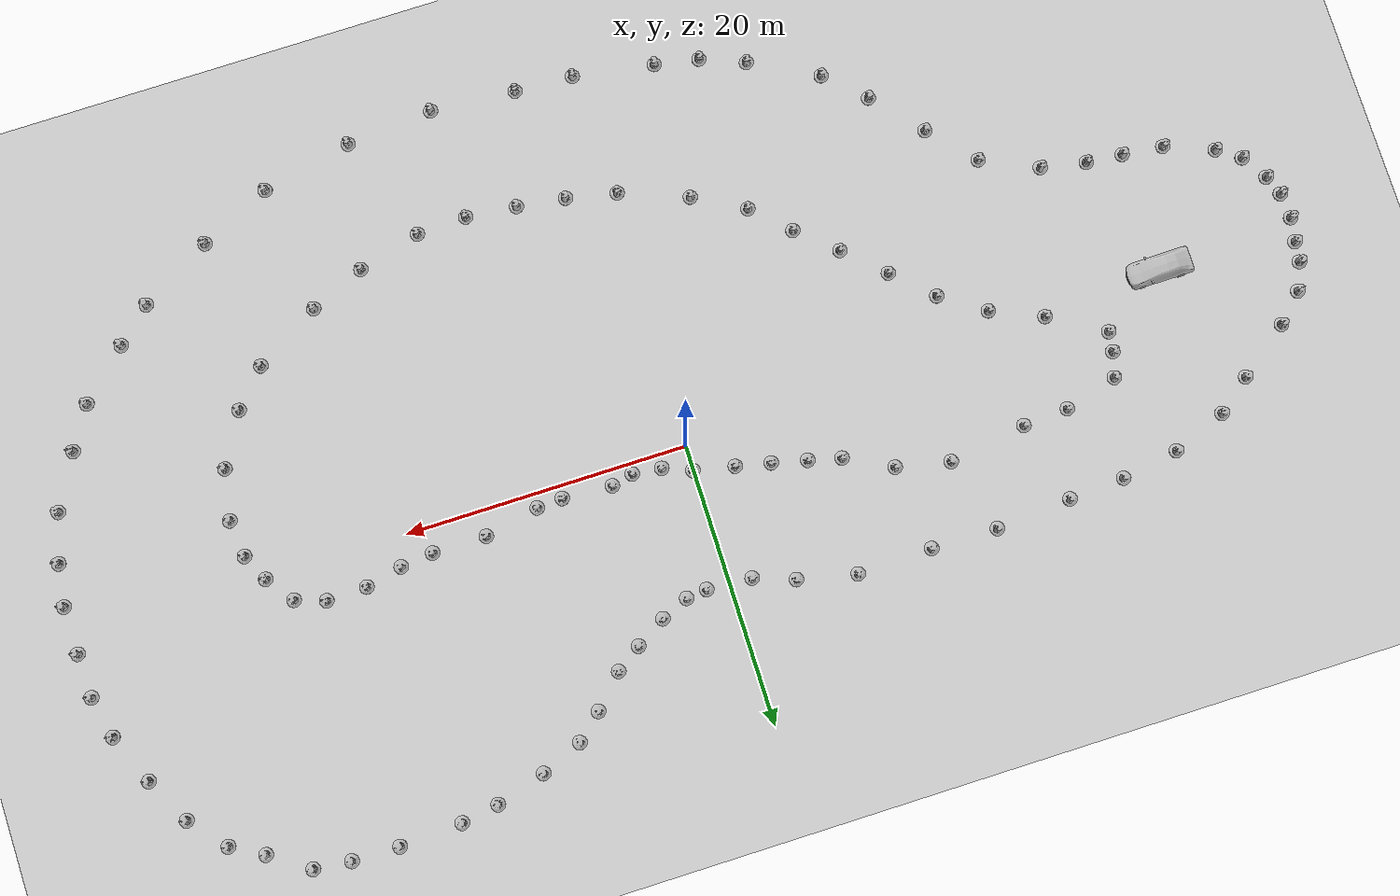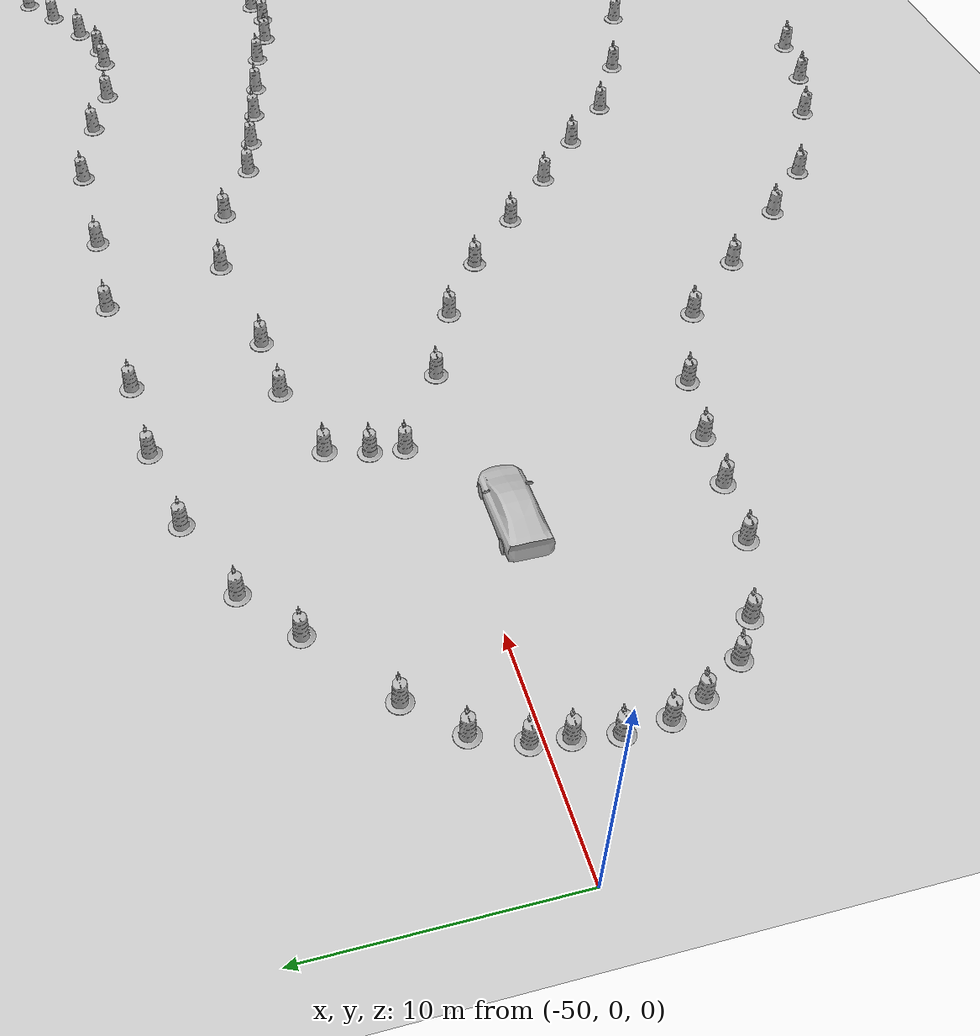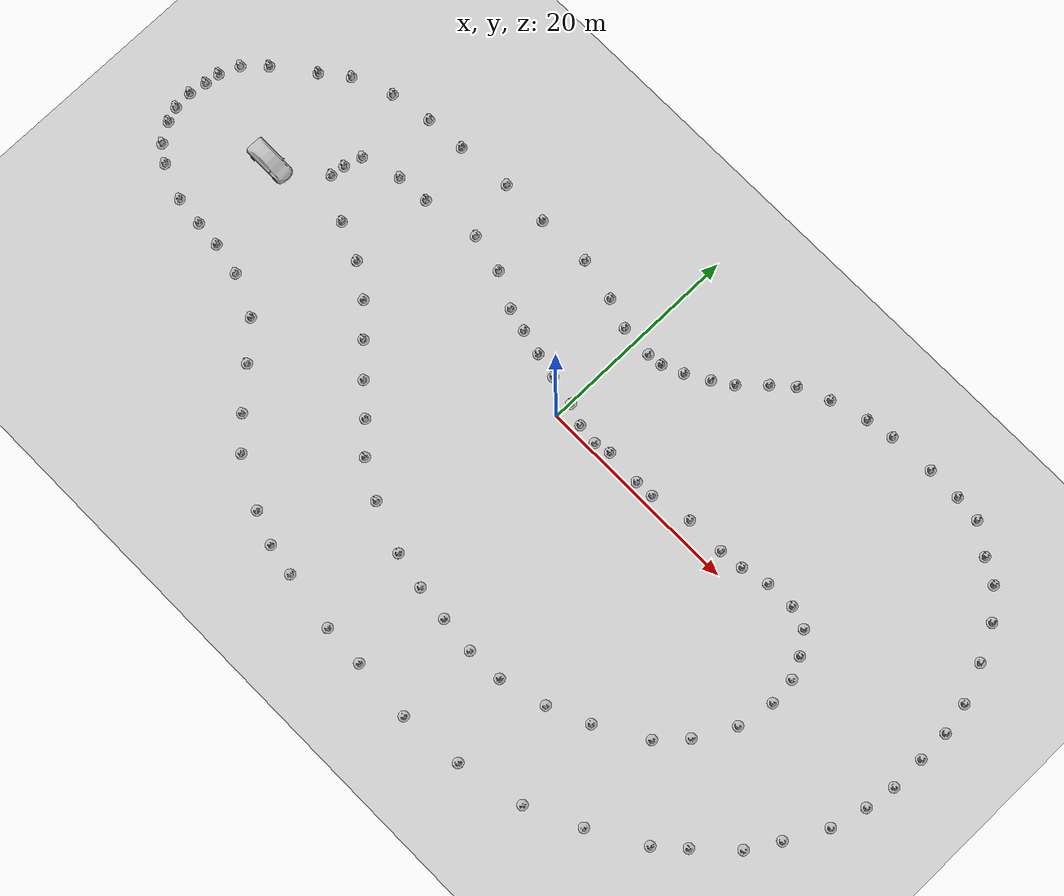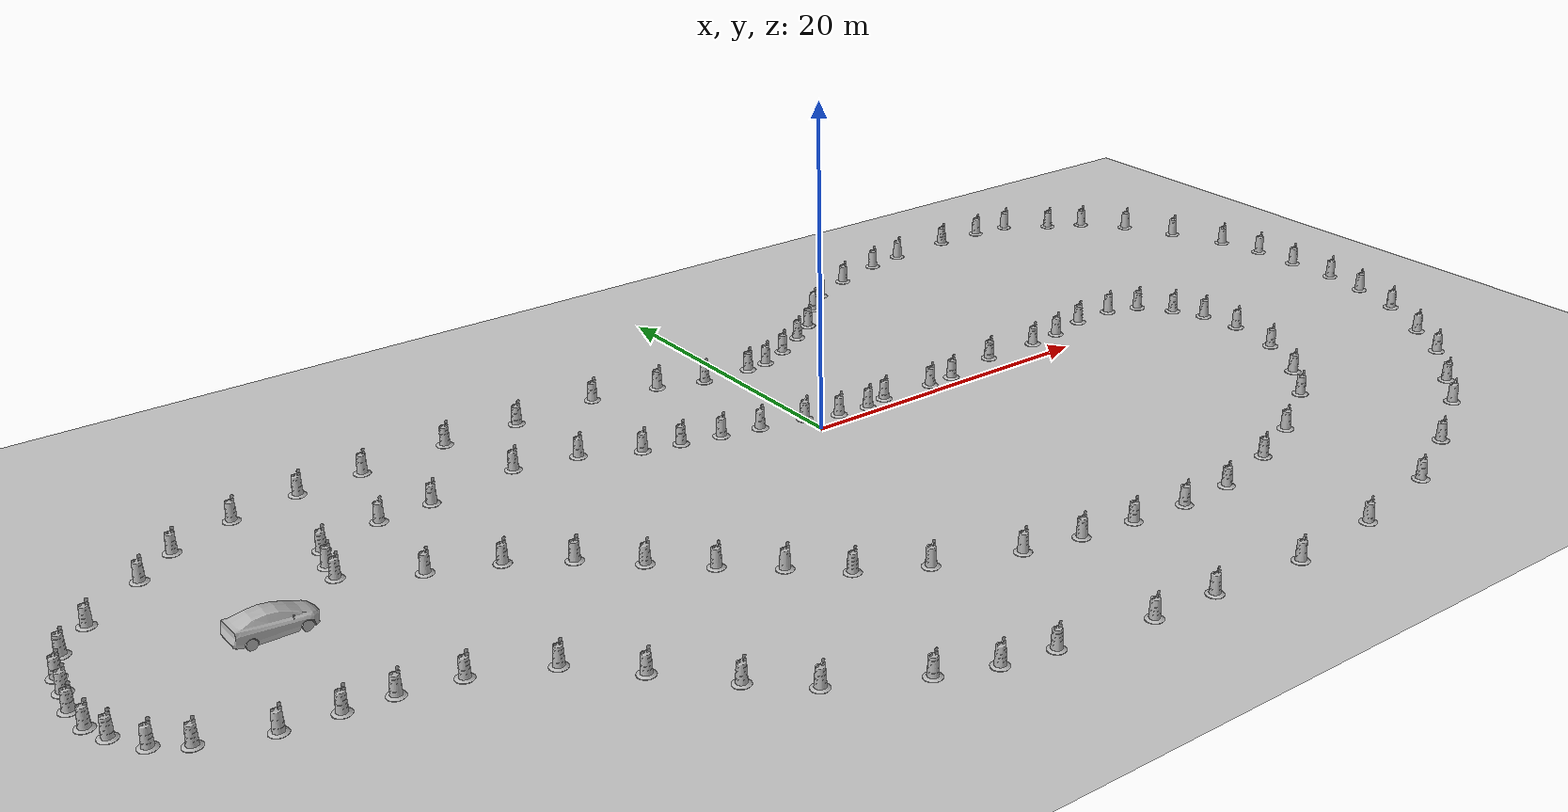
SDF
<sdf version="1.6">
 <world name="default">
  <light name="sun" type="directional">
   <pose>0 0 10 0 -0 0</pose>
   <diffuse>0.8 0.8 0.8 1</diffuse>
   <specular>0.2 0.2 0.2 1</specular>
   <attenuation>
    <range>1000</range>
    <constant>0.9</constant>
    <linear>0.01</linear>
    <quadratic>0.001</quadratic>
   </attenuation>
   <direction>-0.5 0.1 -0.9</direction>
  </light>
  <model name="ground_plane">
   <static>1</static>
   <link name="link">
    <collision name="collision">
     <geometry><plane><normal>0 0 1</normal><size>100 100</size></plane></geometry>
     <surface>
      <contact><collide_bitmask>65535</collide_bitmask></contact>
      <friction><ode><mu>100</mu><mu2>50</mu2></ode></friction>
     </surface>
    </collision>
    <visual name="visual">
     <cast_shadows>0</cast_shadows>
     <geometry><plane><normal>0 0 1</normal><size>100 100</size></plane></geometry>
     <material>
      <script><uri>file://media/materials/scripts/gazebo.material</uri><name>Gazebo/Grey</name></script>
     </material>
    </visual>
   </link>
  </model>
  <model name="prius">
   <link name="base_link">
    <inertial>
     <mass>1</mass>
     <inertia><ixx>0.001</ixx><ixy>0</ixy><ixz>0</ixz><iyy>0.001</iyy><iyz>0</iyz><izz>0.001</izz></inertia>
    </inertial>
   </link>
   <link name="chassis">
    <pose>1.45 0 0 0 -0 1.57</pose>
    <inertial>
     <pose>-0 -0.002735 0.483209 0 -0 1.5708</pose>
     <mass>1371</mass>
     <inertia>
      <ixx>2591.3</ixx>
      <ixy>0.000184475</ixy>
      <ixz>-0.702035</ixz>
      <iyy>651.702</iyy>
      <iyz>2.57872e-06</iyz>
      <izz>2744.57</izz>
     </inertia>
    </inertial>
    <collision name="chassis_collision">
     <pose>0 0.05 0.625 0 -0 0</pose>
     <geometry><box><size>1.7526 2.1 0.95</size></box></geometry>
    </collision>
    <collision name="chassis_fixed_joint_lump__front_bumper_collision_1">
     <pose>0 -2 0.458488 0 -0 0</pose>
     <geometry><box><size>1.33728 0.48 0.566691</size></box></geometry>
    </collision>
    <collision name="chassis_fixed_joint_lump__hood_collision_2">
     <pose>0 -1.90084 0.676305 0.341247 -0 0</pose>
     <geometry><box><size>1.59797 0.493107 0.265468</size></box></geometry>
    </collision>
    <collision name="chassis_fixed_joint_lump__windshield_collision_3">
     <pose>0 -0.875105 1.03227 0.335476 -0 0</pose>
     <geometry><box><size>1.16838 1.65425 0.272347</size></box></geometry>
    </collision>
    <collision name="chassis_fixed_joint_lump__top_front_collision_4">
     <pose>0 0.161236 1.38604 0.13503 -0 0</pose>
     <geometry><box><size>1.27915 0.625988 0.171868</size></box></geometry>
    </collision>
    <collision name="chassis_fixed_joint_lump__top_rear_collision_5">
     <pose>0 0.817696 1.36007 -0.068997 0 0</pose>
     <geometry><box><size>1.28513 0.771189 0.226557</size></box></geometry>
    </collision>
    <collision name="chassis_fixed_joint_lump__rear_window_collision_6">
     <pose>0 1.64053 1.17513 -0.262017 0 0</pose>
     <geometry><box><size>1.26785 1.11634 0.244286</size></box></geometry>
    </collision>
    <collision name="chassis_fixed_joint_lump__trunk_collision_7">
     <pose>0 1.63706 0.88818 0 -0 0</pose>
     <geometry><box><size>1.78806 1.13899 0.482746</size></box></geometry>
    </collision>
    <collision name="chassis_fixed_joint_lump__back_bumper_collision_8">
     <pose>0 2.05445 0.57787 0 -0 0</pose>
     <geometry><box><size>1.78165 0.512093 0.581427</size></box></geometry>
    </collision>
    <visual name="chassis_visual">
     <geometry>
      <mesh><scale>0.01 0.01 0.01</scale><uri>model://../../prius_description/meshes/hybrid_body.obj</uri></mesh>
     </geometry>
    </visual>
    <sensor name="center_laser_sensor" type="ray">
     <ray>
      <scan>
       <horizontal>
        <samples>512</samples>
        <resolution>1</resolution>
        <min_angle>-3.14</min_angle>
        <max_angle>3.14</max_angle>
       </horizontal>
       <vertical><samples>16</samples><min_angle>-0.1</min_angle><max_angle>-0.35</max_angle></vertical>
      </scan>
      <range><min>0.2</min><max>30</max><resolution>0.01</resolution></range>
     </ray>
     <plugin name="center_laser" filename="libgazebo_ros_block_laser.so">
      <topicName>/prius/center_laser/scan</topicName>
      <frameName>center_laser_link</frameName>
      <gaussianNoise>0.01</gaussianNoise>
      <robotNamespace>/</robotNamespace>
     </plugin>
     <always_on>1</always_on>
     <update_rate>30</update_rate>
     <visualize>0</visualize>
     <pose>0 0.4 1.8 0 0 -1.5707</pose>
    </sensor>
    <sensor name="front_camera_sensor" type="camera">
     <update_rate>30</update_rate>
     <camera name="front_camera">
      <horizontal_fov>1.39626</horizontal_fov>
      <image><width>800</width><height>800</height><format>R8G8B8</format></image>
      <clip><near>0.02</near><far>300</far></clip>
      <noise><type>gaussian</type><mean>0</mean><stddev>0.007</stddev></noise>
     </camera>
     <plugin name="front_camera_controller" filename="libgazebo_ros_camera.so">
      <alwaysOn>1</alwaysOn>
      <updateRate>0.0</updateRate>
      <cameraName>/prius/front_camera</cameraName>
      <imageTopicName>image_raw</imageTopicName>
      <cameraInfoTopicName>/prius/front_camera_info</cameraInfoTopicName>
      <frameName>camera_link</frameName>
      <hackBaseline>0.07</hackBaseline>
      <distortionK1>0.0</distortionK1>
      <distortionK2>0.0</distortionK2>
      <distortionK3>0.0</distortionK3>
      <distortionT1>0.0</distortionT1>
      <distortionT2>0.0</distortionT2>
      <robotNamespace>/</robotNamespace>
     </plugin>
     <pose>0 -0.4 1.4 0 0.05 -1.5707</pose>
    </sensor>
   </link>
   <joint name="base_link_connection" type="revolute">
    <child>chassis</child>
    <parent>base_link</parent>
    <axis>
     <limit><lower>0</lower><upper>0</upper></limit>
     <dynamics>
      <damping>0</damping>
      <friction>0</friction>
      <spring_reference>0</spring_reference>
      <spring_stiffness>0</spring_stiffness>
     </dynamics>
     <use_parent_model_frame>1</use_parent_model_frame>
     <xyz>0 0 1</xyz>
    </axis>
    <physics><ode><limit><cfm>0</cfm><erp>0.2</erp></limit></ode></physics>
   </joint>
   <link name="fl_axle">
    <pose>2.86061 0.765877 0.3 0 -0 1.57</pose>
    <inertial>
     <mass>1</mass>
     <inertia><ixx>0.004</ixx><ixy>0</ixy><ixz>0</ixz><iyy>0.004</iyy><iyz>0</iyz><izz>0.004</izz></inertia>
    </inertial>
   </link>
   <joint name="front_left_steer_joint" type="revolute">
    <child>fl_axle</child>
    <parent>chassis</parent>
    <axis>
     <xyz>0 0 1</xyz>
     <limit><lower>-1e+16</lower><upper>1e+16</upper></limit>
     <dynamics><spring_reference>0</spring_reference><spring_stiffness>0</spring_stiffness></dynamics>
     <use_parent_model_frame>1</use_parent_model_frame>
    </axis>
   </joint>
   <link name="front_left_wheel">
    <pose>2.86061 0.765877 0.3 0 -0 1.57</pose>
    <inertial>
     <mass>11</mass>
     <inertia>
      <ixx>0.586312</ixx>
      <ixy>0</ixy>
      <ixz>0</ixz>
      <iyy>0.335529</iyy>
      <iyz>0</iyz>
      <izz>0.335529</izz>
     </inertia>
    </inertial>
    <collision name="front_left_wheel_collision_collision">
     <geometry><sphere><radius>0.31265</radius></sphere></geometry>
     <surface>
      <contact><ode><kp>1e+08</kp><min_depth>0.005</min_depth></ode></contact>
      <friction><ode><mu>0.9</mu><mu2>0.9</mu2></ode></friction>
     </surface>
    </collision>
    <visual name="front_left_wheel_visual">
     <geometry>
      <mesh><scale>0.01 0.01 0.01</scale><uri>model://../../prius_description/meshes/wheel.obj</uri></mesh>
     </geometry>
     <material><script><uri>__default__</uri><name>__default__</name></script></material>
    </visual>
   </link>
   <joint name="front_left_wheel_joint" type="revolute">
    <child>front_left_wheel</child>
    <parent>fl_axle</parent>
    <axis>
     <xyz>0.000796 1 0</xyz>
     <limit><lower>-1e+16</lower><upper>1e+16</upper></limit>
     <dynamics><spring_reference>0</spring_reference><spring_stiffness>0</spring_stiffness></dynamics>
     <use_parent_model_frame>1</use_parent_model_frame>
    </axis>
   </joint>
   <link name="fr_axle">
    <pose>2.85939 -0.768123 0.3 0 -0 1.57</pose>
    <inertial>
     <mass>1</mass>
     <inertia><ixx>0.004</ixx><ixy>0</ixy><ixz>0</ixz><iyy>0.004</iyy><iyz>0</iyz><izz>0.004</izz></inertia>
    </inertial>
   </link>
   <joint name="front_right_steer_joint" type="revolute">
    <child>fr_axle</child>
    <parent>chassis</parent>
    <axis>
     <xyz>0 0 1</xyz>
     <limit><lower>-1e+16</lower><upper>1e+16</upper></limit>
     <dynamics><spring_reference>0</spring_reference><spring_stiffness>0</spring_stiffness></dynamics>
     <use_parent_model_frame>1</use_parent_model_frame>
    </axis>
   </joint>
   <link name="front_right_wheel">
    <pose>2.85939 -0.768123 0.3 0 -0 1.57</pose>
    <inertial>
     <mass>11</mass>
     <inertia>
      <ixx>0.586312</ixx>
      <ixy>0</ixy>
      <ixz>0</ixz>
      <iyy>0.335529</iyy>
      <iyz>0</iyz>
      <izz>0.335529</izz>
     </inertia>
    </inertial>
    <collision name="front_right_wheel_collision_collision">
     <geometry><sphere><radius>0.31265</radius></sphere></geometry>
     <surface>
      <contact><ode><kp>1e+08</kp><min_depth>0.005</min_depth></ode></contact>
      <friction><ode><mu>0.9</mu><mu2>0.9</mu2></ode></friction>
     </surface>
    </collision>
    <visual name="front_right_wheel_visual">
     <geometry>
      <mesh><scale>0.01 0.01 0.01</scale><uri>model://../../prius_description/meshes/wheel.obj</uri></mesh>
     </geometry>
     <material><script><uri>__default__</uri><name>__default__</name></script></material>
    </visual>
   </link>
   <joint name="front_right_wheel_joint" type="revolute">
    <child>front_right_wheel</child>
    <parent>fr_axle</parent>
    <axis>
     <xyz>0.000796 1 0</xyz>
     <limit><lower>-1e+16</lower><upper>1e+16</upper></limit>
     <dynamics><spring_reference>0</spring_reference><spring_stiffness>0</spring_stiffness></dynamics>
     <use_parent_model_frame>1</use_parent_model_frame>
    </axis>
   </joint>
   <link name="rear_left_wheel">
    <pose>0.000632 0.794154 0.3 0 -0 1.57</pose>
    <inertial>
     <mass>11</mass>
     <inertia>
      <ixx>0.586312</ixx>
      <ixy>0</ixy>
      <ixz>0</ixz>
      <iyy>0.335529</iyy>
      <iyz>0</iyz>
      <izz>0.335529</izz>
     </inertia>
    </inertial>
    <collision name="rear_left_wheel_collision_collision">
     <geometry><sphere><radius>0.31265</radius></sphere></geometry>
     <surface>
      <contact><ode><kp>1e+08</kp><min_depth>0.005</min_depth></ode></contact>
      <friction><ode><mu>0.9</mu><mu2>0.9</mu2></ode></friction>
     </surface>
    </collision>
    <visual name="rear_left_wheel_visual">
     <geometry>
      <mesh><scale>0.01 0.01 0.01</scale><uri>model://../../prius_description/meshes/wheel.obj</uri></mesh>
     </geometry>
     <material><script><uri>__default__</uri><name>__default__</name></script></material>
    </visual>
   </link>
   <joint name="rear_left_wheel_joint" type="revolute">
    <child>rear_left_wheel</child>
    <parent>chassis</parent>
    <axis>
     <xyz>0.000796 1 0</xyz>
     <limit><lower>-1e+16</lower><upper>1e+16</upper></limit>
     <dynamics><spring_reference>0</spring_reference><spring_stiffness>0</spring_stiffness></dynamics>
     <use_parent_model_frame>1</use_parent_model_frame>
    </axis>
   </joint>
   <link name="rear_right_wheel">
    <pose>-0.000631 -0.791845 0.3 0 -0 1.57</pose>
    <inertial>
     <mass>11</mass>
     <inertia>
      <ixx>0.586312</ixx>
      <ixy>0</ixy>
      <ixz>0</ixz>
      <iyy>0.335529</iyy>
      <iyz>0</iyz>
      <izz>0.335529</izz>
     </inertia>
    </inertial>
    <collision name="rear_right_wheel_collision_collision">
     <geometry><sphere><radius>0.31265</radius></sphere></geometry>
     <surface>
      <contact><ode><kp>1e+08</kp><min_depth>0.005</min_depth></ode></contact>
      <friction><ode><mu>0.9</mu><mu2>0.9</mu2></ode></friction>
     </surface>
    </collision>
    <visual name="rear_right_wheel_visual">
     <geometry>
      <mesh><scale>0.01 0.01 0.01</scale><uri>model://../../prius_description/meshes/wheel.obj</uri></mesh>
     </geometry>
     <material><script><uri>__default__</uri><name>__default__</name></script></material>
    </visual>
   </link>
   <joint name="rear_right_wheel_joint" type="revolute">
    <child>rear_right_wheel</child>
    <parent>chassis</parent>
    <axis>
     <xyz>0.000796 1 0</xyz>
     <limit><lower>-1e+16</lower><upper>1e+16</upper></limit>
     <dynamics><spring_reference>0</spring_reference><spring_stiffness>0</spring_stiffness></dynamics>
     <use_parent_model_frame>1</use_parent_model_frame>
    </axis>
   </joint>
   <link name="steering_wheel">
    <pose>2.07815 0.357234 0.988243 -1.3021 0 1.57</pose>
    <inertial>
     <mass>1</mass>
     <inertia><ixx>0.145833</ixx><ixy>0</ixy><ixz>0</ixz><iyy>0.145833</iyy><iyz>0</iyz><izz>0.125</izz></inertia>
    </inertial>
    <visual name="steering_wheel_visual">
     <pose>0 0 0 1.3021 -0 0</pose>
     <geometry>
      <mesh><scale>0.01 0.01 0.01</scale><uri>model://../../prius_description/meshes/steering_wheel.obj</uri></mesh>
     </geometry>
    </visual>
   </link>
   <joint name="steering_joint" type="revolute">
    <child>steering_wheel</child>
    <parent>chassis</parent>
    <axis>
     <xyz>-0.964118 0.000768 0.265474</xyz>
     <limit><lower>-1e+16</lower><upper>1e+16</upper></limit>
     <dynamics><spring_reference>0</spring_reference><spring_stiffness>0</spring_stiffness></dynamics>
     <use_parent_model_frame>1</use_parent_model_frame>
    </axis>
   </joint>
   <plugin name="pruis_hybrid_drive" filename="libPriusHybridPlugin.so">
    <chassis>chassis</chassis>
    <front_left_wheel>front_left_wheel_joint</front_left_wheel>
    <front_right_wheel>front_right_wheel_joint</front_right_wheel>
    <front_left_wheel_steering>front_left_steer_joint</front_left_wheel_steering>
    <front_right_wheel_steering>front_right_steer_joint</front_right_wheel_steering>
    <back_left_wheel>rear_left_wheel_joint</back_left_wheel>
    <back_right_wheel>rear_right_wheel_joint</back_right_wheel>
    <steering_wheel>steering_joint</steering_wheel>
    <chassis_aero_force_gain>0.63045</chassis_aero_force_gain>
    <front_torque>859.4004393000001</front_torque>
    <back_torque>0</back_torque>
    <front_brake_torque>1031.28052716</front_brake_torque>
    <back_brake_torque>687.5203514400001</back_brake_torque>
    <max_speed>5</max_speed>
    <min_gas_flow>8.981854013171626e-05</min_gas_flow>
    <gas_efficiency>0.371</gas_efficiency>
    <battery_charge_watt_hours>291</battery_charge_watt_hours>
    <battery_discharge_watt_hours>214</battery_discharge_watt_hours>
    <max_steer>0.6458</max_steer>
    <flwheel_steering_p_gain>1e4</flwheel_steering_p_gain>
    <frwheel_steering_p_gain>1e4</frwheel_steering_p_gain>
    <flwheel_steering_i_gain>0</flwheel_steering_i_gain>
    <frwheel_steering_i_gain>0</frwheel_steering_i_gain>
    <flwheel_steering_d_gain>3e2</flwheel_steering_d_gain>
    <frwheel_steering_d_gain>3e2</frwheel_steering_d_gain>
    <robotNamespace>/</robotNamespace>
   </plugin>
   <plugin name="joint_state_publisher" filename="libgazebo_ros_joint_state_publisher.so">
    <jointName>rear_right_wheel_joint, rear_left_wheel_joint, front_right_wheel_joint, front_left_wheel_joint, front_right_steer_joint, front_left_steer_joint, steering_joint</jointName>
    <updateRate>100.0</updateRate>
    <alwaysOn>1</alwaysOn>
    <robotNamespace>/</robotNamespace>
   </plugin>
   <static>0</static>
   <plugin name="p3d" filename="libgazebo_ros_p3d.so">
    <bodyName>base_link</bodyName>
    <topicName>base_pose_ground_truth</topicName>
    <frameName>map</frameName>
    <updateRate>100.0</updateRate>
    <robotNamespace>/</robotNamespace>
   </plugin>
   <pose>-36.3484 -1.90871 0.006903 0 0.000236 0.002917</pose>
  </model>
  <gravity>0 0 -9.8</gravity>
  <magnetic_field>6e-06 2.3e-05 -4.2e-05</magnetic_field>
  <atmosphere type="adiabatic"/>
  <physics name="default_physics" default="0" type="ode">
   <max_step_size>0.001</max_step_size>
   <real_time_factor>1</real_time_factor>
   <real_time_update_rate>1000</real_time_update_rate>
  </physics>
  <scene><ambient>0.4 0.4 0.4 1</ambient><background>0.7 0.7 0.7 1</background><shadows>1</shadows></scene>
  <spherical_coordinates>
   <surface_model>EARTH_WGS84</surface_model>
   <latitude_deg>0</latitude_deg>
   <longitude_deg>0</longitude_deg>
   <elevation>0</elevation>
   <heading_deg>0</heading_deg>
  </spherical_coordinates>
  <model name="Construction Barrel_0">
   <link name="link">
    <inertial>
     <pose>0 0 0.4 0 -0 0</pose>
     <mass>500</mass>
     <inertia><ixx>51.2096</ixx><iyy>51.2096</iyy><izz>25</izz><ixy>0</ixy><ixz>0</ixz><iyz>0</iyz></inertia>
    </inertial>
    <collision name="collision">
     <geometry><mesh><uri>model://construction_barrel/meshes/construction_barrel.dae</uri></mesh></geometry>
    </collision>
    <visual name="visual">
     <geometry><mesh><uri>model://construction_barrel/meshes/construction_barrel.dae</uri></mesh></geometry>
    </visual>
   </link>
   <pose>-26.441 -1.15652 -2e-06 6e-06 -4e-06 -1.6e-05</pose>
  </model>
  <model name="Construction Barrel_0_clone">
   <link name="link">
    <inertial>
     <pose>0 0 0.4 0 -0 0</pose>
     <mass>500</mass>
     <inertia><ixx>51.2096</ixx><iyy>51.2096</iyy><izz>25</izz><ixy>0</ixy><ixz>0</ixz><iyz>0</iyz></inertia>
    </inertial>
    <collision name="collision">
     <geometry><mesh><uri>model://construction_barrel/meshes/construction_barrel.dae</uri></mesh></geometry>
    </collision>
    <visual name="visual">
     <geometry><mesh><uri>model://construction_barrel/meshes/construction_barrel.dae</uri></mesh></geometry>
    </visual>
   </link>
   <pose>-22.8294 -2.72185 -2e-06 6e-06 -4e-06 -2.1e-05</pose>
  </model>
  <model name="Construction Barrel_0_clone_0">
   <link name="link">
    <inertial>
     <pose>0 0 0.4 0 -0 0</pose>
     <mass>500</mass>
     <inertia><ixx>51.2096</ixx><iyy>51.2096</iyy><izz>25</izz><ixy>0</ixy><ixz>0</ixz><iyz>0</iyz></inertia>
    </inertial>
    <collision name="collision">
     <geometry><mesh><uri>model://construction_barrel/meshes/construction_barrel.dae</uri></mesh></geometry>
    </collision>
    <visual name="visual">
     <geometry><mesh><uri>model://construction_barrel/meshes/construction_barrel.dae</uri></mesh></geometry>
    </visual>
   </link>
   <pose>-19.7578 -4.79895 -2e-06 6e-06 -4e-06 -2.1e-05</pose>
  </model>
  <model name="Construction Barrel_0_clone_1">
   <link name="link">
    <inertial>
     <pose>0 0 0.4 0 -0 0</pose>
     <mass>500</mass>
     <inertia><ixx>51.2096</ixx><iyy>51.2096</iyy><izz>25</izz><ixy>0</ixy><ixz>0</ixz><iyz>0</iyz></inertia>
    </inertial>
    <collision name="collision">
     <geometry><mesh><uri>model://construction_barrel/meshes/construction_barrel.dae</uri></mesh></geometry>
    </collision>
    <visual name="visual">
     <geometry><mesh><uri>model://construction_barrel/meshes/construction_barrel.dae</uri></mesh></geometry>
    </visual>
   </link>
   <pose>-17.0718 -7.34908 -2e-06 6e-06 -4e-06 -2.1e-05</pose>
  </model>
  <model name="Construction Barrel_0_clone_2">
   <link name="link">
    <inertial>
     <pose>0 0 0.4 0 -0 0</pose>
     <mass>500</mass>
     <inertia><ixx>51.2096</ixx><iyy>51.2096</iyy><izz>25</izz><ixy>0</ixy><ixz>0</ixz><iyz>0</iyz></inertia>
    </inertial>
    <collision name="collision">
     <geometry><mesh><uri>model://construction_barrel/meshes/construction_barrel.dae</uri></mesh></geometry>
    </collision>
    <visual name="visual">
     <geometry><mesh><uri>model://construction_barrel/meshes/construction_barrel.dae</uri></mesh></geometry>
    </visual>
   </link>
   <pose>-14.373 -9.88821 -2e-06 6e-06 -4e-06 -2.1e-05</pose>
  </model>
  <model name="Construction Barrel_0_clone_3">
   <link name="link">
    <inertial>
     <pose>0 0 0.4 0 -0 0</pose>
     <mass>500</mass>
     <inertia><ixx>51.2096</ixx><iyy>51.2096</iyy><izz>25</izz><ixy>0</ixy><ixz>0</ixz><iyz>0</iyz></inertia>
    </inertial>
    <collision name="collision">
     <geometry><mesh><uri>model://construction_barrel/meshes/construction_barrel.dae</uri></mesh></geometry>
    </collision>
    <visual name="visual">
     <geometry><mesh><uri>model://construction_barrel/meshes/construction_barrel.dae</uri></mesh></geometry>
    </visual>
   </link>
   <pose>-11.6986 -12.2282 -2e-06 6e-06 -4e-06 -2.1e-05</pose>
  </model>
  <model name="Construction Barrel_0_clone_4">
   <link name="link">
    <inertial>
     <pose>0 0 0.4 0 -0 0</pose>
     <mass>500</mass>
     <inertia><ixx>51.2096</ixx><iyy>51.2096</iyy><izz>25</izz><ixy>0</ixy><ixz>0</ixz><iyz>0</iyz></inertia>
    </inertial>
    <collision name="collision">
     <geometry><mesh><uri>model://construction_barrel/meshes/construction_barrel.dae</uri></mesh></geometry>
    </collision>
    <visual name="visual">
     <geometry><mesh><uri>model://construction_barrel/meshes/construction_barrel.dae</uri></mesh></geometry>
    </visual>
   </link>
   <pose>-9.18742 -14.6506 -2e-06 6e-06 -4e-06 -2.1e-05</pose>
  </model>
  <model name="Construction Barrel_0_clone_5">
   <link name="link">
    <inertial>
     <pose>0 0 0.4 0 -0 0</pose>
     <mass>500</mass>
     <inertia><ixx>51.2096</ixx><iyy>51.2096</iyy><izz>25</izz><ixy>0</ixy><ixz>0</ixz><iyz>0</iyz></inertia>
    </inertial>
    <collision name="collision">
     <geometry><mesh><uri>model://construction_barrel/meshes/construction_barrel.dae</uri></mesh></geometry>
    </collision>
    <visual name="visual">
     <geometry><mesh><uri>model://construction_barrel/meshes/construction_barrel.dae</uri></mesh></geometry>
    </visual>
   </link>
   <pose>-5.61931 -16.6517 -2e-06 6e-06 -4e-06 -2.1e-05</pose>
  </model>
  <model name="Construction Barrel_0_clone_6">
   <link name="link">
    <inertial>
     <pose>0 0 0.4 0 -0 0</pose>
     <mass>500</mass>
     <inertia><ixx>51.2096</ixx><iyy>51.2096</iyy><izz>25</izz><ixy>0</ixy><ixz>0</ixz><iyz>0</iyz></inertia>
    </inertial>
    <collision name="collision">
     <geometry><mesh><uri>model://construction_barrel/meshes/construction_barrel.dae</uri></mesh></geometry>
    </collision>
    <visual name="visual">
     <geometry><mesh><uri>model://construction_barrel/meshes/construction_barrel.dae</uri></mesh></geometry>
    </visual>
   </link>
   <pose>-0.864448 -18.4838 -2e-06 6e-06 -4e-06 -2.1e-05</pose>
  </model>
  <model name="Construction Barrel_0_clone_7">
   <link name="link">
    <inertial>
     <pose>0 0 0.4 0 -0 0</pose>
     <mass>500</mass>
     <inertia><ixx>51.2096</ixx><iyy>51.2096</iyy><izz>25</izz><ixy>0</ixy><ixz>0</ixz><iyz>0</iyz></inertia>
    </inertial>
    <collision name="collision">
     <geometry><mesh><uri>model://construction_barrel/meshes/construction_barrel.dae</uri></mesh></geometry>
    </collision>
    <visual name="visual">
     <geometry><mesh><uri>model://construction_barrel/meshes/construction_barrel.dae</uri></mesh></geometry>
    </visual>
   </link>
   <pose>6.11324 -19.6723 -2e-06 6e-06 -4e-06 -2.1e-05</pose>
  </model>
  <model name="Construction Barrel_0_clone_8">
   <link name="link">
    <inertial>
     <pose>0 0 0.4 0 -0 0</pose>
     <mass>500</mass>
     <inertia><ixx>51.2096</ixx><iyy>51.2096</iyy><izz>25</izz><ixy>0</ixy><ixz>0</ixz><iyz>0</iyz></inertia>
    </inertial>
    <collision name="collision">
     <geometry><mesh><uri>model://construction_barrel/meshes/construction_barrel.dae</uri></mesh></geometry>
    </collision>
    <visual name="visual">
     <geometry><mesh><uri>model://construction_barrel/meshes/construction_barrel.dae</uri></mesh></geometry>
    </visual>
   </link>
   <pose>13.2531 -19.884 -2e-06 6e-06 -4e-06 -2.1e-05</pose>
  </model>
  <model name="Construction Barrel_0_clone_9">
   <link name="link">
    <inertial>
     <pose>0 0 0.4 0 -0 0</pose>
     <mass>500</mass>
     <inertia><ixx>51.2096</ixx><iyy>51.2096</iyy><izz>25</izz><ixy>0</ixy><ixz>0</ixz><iyz>0</iyz></inertia>
    </inertial>
    <collision name="collision">
     <geometry><mesh><uri>model://construction_barrel/meshes/construction_barrel.dae</uri></mesh></geometry>
    </collision>
    <visual name="visual">
     <geometry><mesh><uri>model://construction_barrel/meshes/construction_barrel.dae</uri></mesh></geometry>
    </visual>
   </link>
   <pose>2.67529 -19.2111 -2e-06 6e-06 -4e-06 -2.1e-05</pose>
  </model>
  <model name="Construction Barrel_0_clone_10">
   <link name="link">
    <inertial>
     <pose>0 0 0.4 0 -0 0</pose>
     <mass>500</mass>
     <inertia><ixx>51.2096</ixx><iyy>51.2096</iyy><izz>25</izz><ixy>0</ixy><ixz>0</ixz><iyz>0</iyz></inertia>
    </inertial>
    <collision name="collision">
     <geometry><mesh><uri>model://construction_barrel/meshes/construction_barrel.dae</uri></mesh></geometry>
    </collision>
    <visual name="visual">
     <geometry><mesh><uri>model://construction_barrel/meshes/construction_barrel.dae</uri></mesh></geometry>
    </visual>
   </link>
   <pose>9.69936 -20.0233 -2e-06 6e-06 -4e-06 -2.1e-05</pose>
  </model>
  <model name="Construction Barrel_0_clone_11">
   <link name="link">
    <inertial>
     <pose>0 0 0.4 0 -0 0</pose>
     <mass>500</mass>
     <inertia><ixx>51.2096</ixx><iyy>51.2096</iyy><izz>25</izz><ixy>0</ixy><ixz>0</ixz><iyz>0</iyz></inertia>
    </inertial>
    <collision name="collision">
     <geometry><mesh><uri>model://construction_barrel/meshes/construction_barrel.dae</uri></mesh></geometry>
    </collision>
    <visual name="visual">
     <geometry><mesh><uri>model://construction_barrel/meshes/construction_barrel.dae</uri></mesh></geometry>
    </visual>
   </link>
   <pose>17.7118 -18.6691 -2e-06 6e-06 -4e-06 -2.1e-05</pose>
  </model>
  <model name="Construction Barrel_0_clone_12">
   <link name="link">
    <inertial>
     <pose>0 0 0.4 0 -0 0</pose>
     <mass>500</mass>
     <inertia><ixx>51.2096</ixx><iyy>51.2096</iyy><izz>25</izz><ixy>0</ixy><ixz>0</ixz><iyz>0</iyz></inertia>
    </inertial>
    <collision name="collision">
     <geometry><mesh><uri>model://construction_barrel/meshes/construction_barrel.dae</uri></mesh></geometry>
    </collision>
    <visual name="visual">
     <geometry><mesh><uri>model://construction_barrel/meshes/construction_barrel.dae</uri></mesh></geometry>
    </visual>
   </link>
   <pose>21.6119 -17.0011 -2e-06 6e-06 -4e-06 -2.1e-05</pose>
  </model>
  <model name="Construction Barrel_0_clone_13">
   <link name="link">
    <inertial>
     <pose>0 0 0.4 0 -0 0</pose>
     <mass>500</mass>
     <inertia><ixx>51.2096</ixx><iyy>51.2096</iyy><izz>25</izz><ixy>0</ixy><ixz>0</ixz><iyz>0</iyz></inertia>
    </inertial>
    <collision name="collision">
     <geometry><mesh><uri>model://construction_barrel/meshes/construction_barrel.dae</uri></mesh></geometry>
    </collision>
    <visual name="visual">
     <geometry><mesh><uri>model://construction_barrel/meshes/construction_barrel.dae</uri></mesh></geometry>
    </visual>
   </link>
   <pose>26.2211 -14.2448 -2e-06 6e-06 -4e-06 -2.1e-05</pose>
  </model>
  <model name="Construction Barrel_0_clone_14">
   <link name="link">
    <inertial>
     <pose>0 0 0.4 0 -0 0</pose>
     <mass>500</mass>
     <inertia><ixx>51.2096</ixx><iyy>51.2096</iyy><izz>25</izz><ixy>0</ixy><ixz>0</ixz><iyz>0</iyz></inertia>
    </inertial>
    <collision name="collision">
     <geometry><mesh><uri>model://construction_barrel/meshes/construction_barrel.dae</uri></mesh></geometry>
    </collision>
    <visual name="visual">
     <geometry><mesh><uri>model://construction_barrel/meshes/construction_barrel.dae</uri></mesh></geometry>
    </visual>
   </link>
   <pose>28.5101 -11.7335 -2e-06 6e-06 -4e-06 -2.1e-05</pose>
  </model>
  <model name="Construction Barrel_0_clone_15">
   <link name="link">
    <inertial>
     <pose>0 0 0.4 0 -0 0</pose>
     <mass>500</mass>
     <inertia><ixx>51.2096</ixx><iyy>51.2096</iyy><izz>25</izz><ixy>0</ixy><ixz>0</ixz><iyz>0</iyz></inertia>
    </inertial>
    <collision name="collision">
     <geometry><mesh><uri>model://construction_barrel/meshes/construction_barrel.dae</uri></mesh></geometry>
    </collision>
    <visual name="visual">
     <geometry><mesh><uri>model://construction_barrel/meshes/construction_barrel.dae</uri></mesh></geometry>
    </visual>
   </link>
   <pose>30.5687 -8.10844 -2e-06 6e-06 -4e-06 -2.1e-05</pose>
  </model>
  <model name="Construction Barrel_0_clone_16">
   <link name="link">
    <inertial>
     <pose>0 0 0.4 0 -0 0</pose>
     <mass>500</mass>
     <inertia><ixx>51.2096</ixx><iyy>51.2096</iyy><izz>25</izz><ixy>0</ixy><ixz>0</ixz><iyz>0</iyz></inertia>
    </inertial>
    <collision name="collision">
     <geometry><mesh><uri>model://construction_barrel/meshes/construction_barrel.dae</uri></mesh></geometry>
    </collision>
    <visual name="visual">
     <geometry><mesh><uri>model://construction_barrel/meshes/construction_barrel.dae</uri></mesh></geometry>
    </visual>
   </link>
   <pose>31.2399 -4.56732 -2e-06 6e-06 -4e-06 -2.1e-05</pose>
  </model>
  <model name="Construction Barrel_0_clone_17">
   <link name="link">
    <inertial>
     <pose>0 0 0.4 0 -0 0</pose>
     <mass>500</mass>
     <inertia><ixx>51.2096</ixx><iyy>51.2096</iyy><izz>25</izz><ixy>0</ixy><ixz>0</ixz><iyz>0</iyz></inertia>
    </inertial>
    <collision name="collision">
     <geometry><mesh><uri>model://construction_barrel/meshes/construction_barrel.dae</uri></mesh></geometry>
    </collision>
    <visual name="visual">
     <geometry><mesh><uri>model://construction_barrel/meshes/construction_barrel.dae</uri></mesh></geometry>
    </visual>
   </link>
   <pose>30.9667 -1.92255 -2e-06 6e-06 -4e-06 -2.1e-05</pose>
  </model>
  <model name="Construction Barrel_0_clone_20">
   <link name="link">
    <inertial>
     <pose>0 0 0.4 0 -0 0</pose>
     <mass>500</mass>
     <inertia><ixx>51.2096</ixx><iyy>51.2096</iyy><izz>25</izz><ixy>0</ixy><ixz>0</ixz><iyz>0</iyz></inertia>
    </inertial>
    <collision name="collision">
     <geometry><mesh><uri>model://construction_barrel/meshes/construction_barrel.dae</uri></mesh></geometry>
    </collision>
    <visual name="visual">
     <geometry><mesh><uri>model://construction_barrel/meshes/construction_barrel.dae</uri></mesh></geometry>
    </visual>
   </link>
   <pose>-25.5819 -13.1081 -2e-06 6e-06 -4e-06 -2.1e-05</pose>
  </model>
  <model name="Construction Barrel_0_clone_21">
   <link name="link">
    <inertial>
     <pose>0 0 0.4 0 -0 0</pose>
     <mass>500</mass>
     <inertia><ixx>51.2096</ixx><iyy>51.2096</iyy><izz>25</izz><ixy>0</ixy><ixz>0</ixz><iyz>0</iyz></inertia>
    </inertial>
    <collision name="collision">
     <geometry><mesh><uri>model://construction_barrel/meshes/construction_barrel.dae</uri></mesh></geometry>
    </collision>
    <visual name="visual">
     <geometry><mesh><uri>model://construction_barrel/meshes/construction_barrel.dae</uri></mesh></geometry>
    </visual>
   </link>
   <pose>-22.7053 -16.231 -2e-06 6e-06 -4e-06 -2.1e-05</pose>
  </model>
  <model name="Construction Barrel_0_clone_22">
   <link name="link">
    <inertial>
     <pose>0 0 0.4 0 -0 0</pose>
     <mass>500</mass>
     <inertia><ixx>51.2096</ixx><iyy>51.2096</iyy><izz>25</izz><ixy>0</ixy><ixz>0</ixz><iyz>0</iyz></inertia>
    </inertial>
    <collision name="collision">
     <geometry><mesh><uri>model://construction_barrel/meshes/construction_barrel.dae</uri></mesh></geometry>
    </collision>
    <visual name="visual">
     <geometry><mesh><uri>model://construction_barrel/meshes/construction_barrel.dae</uri></mesh></geometry>
    </visual>
   </link>
   <pose>-19.6719 -19.6475 -2e-06 6e-06 -4e-06 -2.1e-05</pose>
  </model>
  <model name="Construction Barrel_0_clone_23">
   <link name="link">
    <inertial>
     <pose>0 0 0.4 0 -0 0</pose>
     <mass>500</mass>
     <inertia><ixx>51.2096</ixx><iyy>51.2096</iyy><izz>25</izz><ixy>0</ixy><ixz>0</ixz><iyz>0</iyz></inertia>
    </inertial>
    <collision name="collision">
     <geometry><mesh><uri>model://construction_barrel/meshes/construction_barrel.dae</uri></mesh></geometry>
    </collision>
    <visual name="visual">
     <geometry><mesh><uri>model://construction_barrel/meshes/construction_barrel.dae</uri></mesh></geometry>
    </visual>
   </link>
   <pose>-17.0162 -22.1889 -2e-06 6e-06 -4e-06 -2.1e-05</pose>
  </model>
  <model name="Construction Barrel_0_clone_24">
   <link name="link">
    <inertial>
     <pose>0 0 0.4 0 -0 0</pose>
     <mass>500</mass>
     <inertia><ixx>51.2096</ixx><iyy>51.2096</iyy><izz>25</izz><ixy>0</ixy><ixz>0</ixz><iyz>0</iyz></inertia>
    </inertial>
    <collision name="collision">
     <geometry><mesh><uri>model://construction_barrel/meshes/construction_barrel.dae</uri></mesh></geometry>
    </collision>
    <visual name="visual">
     <geometry><mesh><uri>model://construction_barrel/meshes/construction_barrel.dae</uri></mesh></geometry>
    </visual>
   </link>
   <pose>-12.3084 -24.6958 -2e-06 6e-06 -4e-06 -2.1e-05</pose>
  </model>
  <model name="Construction Barrel_0_clone_25">
   <link name="link">
    <inertial>
     <pose>0 0 0.4 0 -0 0</pose>
     <mass>500</mass>
     <inertia><ixx>51.2096</ixx><iyy>51.2096</iyy><izz>25</izz><ixy>0</ixy><ixz>0</ixz><iyz>0</iyz></inertia>
    </inertial>
    <collision name="collision">
     <geometry><mesh><uri>model://construction_barrel/meshes/construction_barrel.dae</uri></mesh></geometry>
    </collision>
    <visual name="visual">
     <geometry><mesh><uri>model://construction_barrel/meshes/construction_barrel.dae</uri></mesh></geometry>
    </visual>
   </link>
   <pose>-6.10313 -26.5127 -2e-06 6e-06 -4e-06 -2.1e-05</pose>
  </model>
  <model name="Construction Barrel_0_clone_26">
   <link name="link">
    <inertial>
     <pose>0 0 0.4 0 -0 0</pose>
     <mass>500</mass>
     <inertia><ixx>51.2096</ixx><iyy>51.2096</iyy><izz>25</izz><ixy>0</ixy><ixz>0</ixz><iyz>0</iyz></inertia>
    </inertial>
    <collision name="collision">
     <geometry><mesh><uri>model://construction_barrel/meshes/construction_barrel.dae</uri></mesh></geometry>
    </collision>
    <visual name="visual">
     <geometry><mesh><uri>model://construction_barrel/meshes/construction_barrel.dae</uri></mesh></geometry>
    </visual>
   </link>
   <pose>-0.370923 -27.4351 -2e-06 6e-06 -4e-06 -2.1e-05</pose>
  </model>
  <model name="Construction Barrel_0_clone_27">
   <link name="link">
    <inertial>
     <pose>0 0 0.4 0 -0 0</pose>
     <mass>500</mass>
     <inertia><ixx>51.2096</ixx><iyy>51.2096</iyy><izz>25</izz><ixy>0</ixy><ixz>0</ixz><iyz>0</iyz></inertia>
    </inertial>
    <collision name="collision">
     <geometry><mesh><uri>model://construction_barrel/meshes/construction_barrel.dae</uri></mesh></geometry>
    </collision>
    <visual name="visual">
     <geometry><mesh><uri>model://construction_barrel/meshes/construction_barrel.dae</uri></mesh></geometry>
    </visual>
   </link>
   <pose>-9.21123 -25.9371 -2e-06 6e-06 -4e-06 -2.1e-05</pose>
  </model>
  <model name="Construction Barrel_0_clone_28">
   <link name="link">
    <inertial>
     <pose>0 0 0.4 0 -0 0</pose>
     <mass>500</mass>
     <inertia><ixx>51.2096</ixx><iyy>51.2096</iyy><izz>25</izz><ixy>0</ixy><ixz>0</ixz><iyz>0</iyz></inertia>
    </inertial>
    <collision name="collision">
     <geometry><mesh><uri>model://construction_barrel/meshes/construction_barrel.dae</uri></mesh></geometry>
    </collision>
    <visual name="visual">
     <geometry><mesh><uri>model://construction_barrel/meshes/construction_barrel.dae</uri></mesh></geometry>
    </visual>
   </link>
   <pose>3.77722 -27.623 -2e-06 6e-06 -4e-06 -2.1e-05</pose>
  </model>
  <model name="Construction Barrel_0_clone_29">
   <link name="link">
    <inertial>
     <pose>0 0 0.4 0 -0 0</pose>
     <mass>500</mass>
     <inertia><ixx>51.2096</ixx><iyy>51.2096</iyy><izz>25</izz><ixy>0</ixy><ixz>0</ixz><iyz>0</iyz></inertia>
    </inertial>
    <collision name="collision">
     <geometry><mesh><uri>model://construction_barrel/meshes/construction_barrel.dae</uri></mesh></geometry>
    </collision>
    <visual name="visual">
     <geometry><mesh><uri>model://construction_barrel/meshes/construction_barrel.dae</uri></mesh></geometry>
    </visual>
   </link>
   <pose>9.82969 -28.0534 -2e-06 6e-06 -4e-06 -2.1e-05</pose>
  </model>
  <model name="Construction Barrel_0_clone_30">
   <link name="link">
    <inertial>
     <pose>0 0 0.4 0 -0 0</pose>
     <mass>500</mass>
     <inertia><ixx>51.2096</ixx><iyy>51.2096</iyy><izz>25</izz><ixy>0</ixy><ixz>0</ixz><iyz>0</iyz></inertia>
    </inertial>
    <collision name="collision">
     <geometry><mesh><uri>model://construction_barrel/meshes/construction_barrel.dae</uri></mesh></geometry>
    </collision>
    <visual name="visual">
     <geometry><mesh><uri>model://construction_barrel/meshes/construction_barrel.dae</uri></mesh></geometry>
    </visual>
   </link>
   <pose>16.0139 -27.507 -2e-06 6e-06 -4e-06 -2.1e-05</pose>
  </model>
  <model name="Construction Barrel_0_clone_31">
   <link name="link">
    <inertial>
     <pose>0 0 0.4 0 -0 0</pose>
     <mass>500</mass>
     <inertia><ixx>51.2096</ixx><iyy>51.2096</iyy><izz>25</izz><ixy>0</ixy><ixz>0</ixz><iyz>0</iyz></inertia>
    </inertial>
    <collision name="collision">
     <geometry><mesh><uri>model://construction_barrel/meshes/construction_barrel.dae</uri></mesh></geometry>
    </collision>
    <visual name="visual">
     <geometry><mesh><uri>model://construction_barrel/meshes/construction_barrel.dae</uri></mesh></geometry>
    </visual>
   </link>
   <pose>22.464 -26.0788 -2e-06 6e-06 -4e-06 -2.1e-05</pose>
  </model>
  <model name="Construction Barrel_0_clone_32">
   <link name="link">
    <inertial>
     <pose>0 0 0.4 0 -0 0</pose>
     <mass>500</mass>
     <inertia><ixx>51.2096</ixx><iyy>51.2096</iyy><izz>25</izz><ixy>0</ixy><ixz>0</ixz><iyz>0</iyz></inertia>
    </inertial>
    <collision name="collision">
     <geometry><mesh><uri>model://construction_barrel/meshes/construction_barrel.dae</uri></mesh></geometry>
    </collision>
    <visual name="visual">
     <geometry><mesh><uri>model://construction_barrel/meshes/construction_barrel.dae</uri></mesh></geometry>
    </visual>
   </link>
   <pose>27.5111 -23.6897 -2e-06 6e-06 -4e-06 -2.1e-05</pose>
  </model>
  <model name="Construction Barrel_0_clone_33">
   <link name="link">
    <inertial>
     <pose>0 0 0.4 0 -0 0</pose>
     <mass>500</mass>
     <inertia><ixx>51.2096</ixx><iyy>51.2096</iyy><izz>25</izz><ixy>0</ixy><ixz>0</ixz><iyz>0</iyz></inertia>
    </inertial>
    <collision name="collision">
     <geometry><mesh><uri>model://construction_barrel/meshes/construction_barrel.dae</uri></mesh></geometry>
    </collision>
    <visual name="visual">
     <geometry><mesh><uri>model://construction_barrel/meshes/construction_barrel.dae</uri></mesh></geometry>
    </visual>
   </link>
   <pose>32.5808 -20.7641 -2e-06 6e-06 -4e-06 -2.1e-05</pose>
  </model>
  <model name="Construction Barrel_0_clone_34">
   <link name="link">
    <inertial>
     <pose>0 0 0.4 0 -0 0</pose>
     <mass>500</mass>
     <inertia><ixx>51.2096</ixx><iyy>51.2096</iyy><izz>25</izz><ixy>0</ixy><ixz>0</ixz><iyz>0</iyz></inertia>
    </inertial>
    <collision name="collision">
     <geometry><mesh><uri>model://construction_barrel/meshes/construction_barrel.dae</uri></mesh></geometry>
    </collision>
    <visual name="visual">
     <geometry><mesh><uri>model://construction_barrel/meshes/construction_barrel.dae</uri></mesh></geometry>
    </visual>
   </link>
   <pose>35.0139 -18.5417 -2e-06 6e-06 -4e-06 -2.1e-05</pose>
  </model>
  <model name="Construction Barrel_0_clone_35">
   <link name="link">
    <inertial>
     <pose>0 0 0.4 0 -0 0</pose>
     <mass>500</mass>
     <inertia><ixx>51.2096</ixx><iyy>51.2096</iyy><izz>25</izz><ixy>0</ixy><ixz>0</ixz><iyz>0</iyz></inertia>
    </inertial>
    <collision name="collision">
     <geometry><mesh><uri>model://construction_barrel/meshes/construction_barrel.dae</uri></mesh></geometry>
    </collision>
    <visual name="visual">
     <geometry><mesh><uri>model://construction_barrel/meshes/construction_barrel.dae</uri></mesh></geometry>
    </visual>
   </link>
   <pose>38.3716 -15.3204 -2e-06 6e-06 -4e-06 -2.1e-05</pose>
  </model>
  <model name="Construction Barrel_0_clone_36">
   <link name="link">
    <inertial>
     <pose>0 0 0.4 0 -0 0</pose>
     <mass>500</mass>
     <inertia><ixx>51.2096</ixx><iyy>51.2096</iyy><izz>25</izz><ixy>0</ixy><ixz>0</ixz><iyz>0</iyz></inertia>
    </inertial>
    <collision name="collision">
     <geometry><mesh><uri>model://construction_barrel/meshes/construction_barrel.dae</uri></mesh></geometry>
    </collision>
    <visual name="visual">
     <geometry><mesh><uri>model://construction_barrel/meshes/construction_barrel.dae</uri></mesh></geometry>
    </visual>
   </link>
   <pose>40.1574 -12.4211 -2e-06 6e-06 -4e-06 -2.1e-05</pose>
  </model>
  <model name="Construction Barrel_0_clone_37">
   <link name="link">
    <inertial>
     <pose>0 0 0.4 0 -0 0</pose>
     <mass>500</mass>
     <inertia><ixx>51.2096</ixx><iyy>51.2096</iyy><izz>25</izz><ixy>0</ixy><ixz>0</ixz><iyz>0</iyz></inertia>
    </inertial>
    <collision name="collision">
     <geometry><mesh><uri>model://construction_barrel/meshes/construction_barrel.dae</uri></mesh></geometry>
    </collision>
    <visual name="visual">
     <geometry><mesh><uri>model://construction_barrel/meshes/construction_barrel.dae</uri></mesh></geometry>
    </visual>
   </link>
   <pose>42.2531 -8.67945 -2e-06 6e-06 -4e-06 -2.1e-05</pose>
  </model>
  <model name="Construction Barrel_0_clone_38">
   <link name="link">
    <inertial>
     <pose>0 0 0.4 0 -0 0</pose>
     <mass>500</mass>
     <inertia><ixx>51.2096</ixx><iyy>51.2096</iyy><izz>25</izz><ixy>0</ixy><ixz>0</ixz><iyz>0</iyz></inertia>
    </inertial>
    <collision name="collision">
     <geometry><mesh><uri>model://construction_barrel/meshes/construction_barrel.dae</uri></mesh></geometry>
    </collision>
    <visual name="visual">
     <geometry><mesh><uri>model://construction_barrel/meshes/construction_barrel.dae</uri></mesh></geometry>
    </visual>
   </link>
   <pose>43.182 -5.26645 -2e-06 6e-06 -4e-06 -2.1e-05</pose>
  </model>
  <model name="Construction Barrel_0_clone_39">
   <link name="link">
    <inertial>
     <pose>0 0 0.4 0 -0 0</pose>
     <mass>500</mass>
     <inertia><ixx>51.2096</ixx><iyy>51.2096</iyy><izz>25</izz><ixy>0</ixy><ixz>0</ixz><iyz>0</iyz></inertia>
    </inertial>
    <collision name="collision">
     <geometry><mesh><uri>model://construction_barrel/meshes/construction_barrel.dae</uri></mesh></geometry>
    </collision>
    <visual name="visual">
     <geometry><mesh><uri>model://construction_barrel/meshes/construction_barrel.dae</uri></mesh></geometry>
    </visual>
   </link>
   <pose>43.6252 -2.32087 -2e-06 6e-06 -4e-06 -2.1e-05</pose>
  </model>
  <model name="Construction Barrel_0_clone_46">
   <link name="link">
    <inertial>
     <pose>0 0 0.4 0 -0 0</pose>
     <mass>500</mass>
     <inertia><ixx>51.2096</ixx><iyy>51.2096</iyy><izz>25</izz><ixy>0</ixy><ixz>0</ixz><iyz>0</iyz></inertia>
    </inertial>
    <collision name="collision">
     <geometry><mesh><uri>model://construction_barrel/meshes/construction_barrel.dae</uri></mesh></geometry>
    </collision>
    <visual name="visual">
     <geometry><mesh><uri>model://construction_barrel/meshes/construction_barrel.dae</uri></mesh></geometry>
    </visual>
   </link>
   <pose>30.0267 0.018624 -2e-06 6e-06 -4e-06 -4.3e-05</pose>
  </model>
  <model name="Construction Barrel_0_clone_47">
   <link name="link">
    <inertial>
     <pose>0 0 0.4 0 -0 0</pose>
     <mass>500</mass>
     <inertia><ixx>51.2096</ixx><iyy>51.2096</iyy><izz>25</izz><ixy>0</ixy><ixz>0</ixz><iyz>0</iyz></inertia>
    </inertial>
    <collision name="collision">
     <geometry><mesh><uri>model://construction_barrel/meshes/construction_barrel.dae</uri></mesh></geometry>
    </collision>
    <visual name="visual">
     <geometry><mesh><uri>model://construction_barrel/meshes/construction_barrel.dae</uri></mesh></geometry>
    </visual>
   </link>
   <pose>28.5899 1.96732 -2e-06 6e-06 -4e-06 -4.3e-05</pose>
  </model>
  <model name="Construction Barrel_0_clone_48">
   <link name="link">
    <inertial>
     <pose>0 0 0.4 0 -0 0</pose>
     <mass>500</mass>
     <inertia><ixx>51.2096</ixx><iyy>51.2096</iyy><izz>25</izz><ixy>0</ixy><ixz>0</ixz><iyz>0</iyz></inertia>
    </inertial>
    <collision name="collision">
     <geometry><mesh><uri>model://construction_barrel/meshes/construction_barrel.dae</uri></mesh></geometry>
    </collision>
    <visual name="visual">
     <geometry><mesh><uri>model://construction_barrel/meshes/construction_barrel.dae</uri></mesh></geometry>
    </visual>
   </link>
   <pose>26.4794 2.67623 -2e-06 6e-06 -4e-06 -4.3e-05</pose>
  </model>
  <model name="Construction Barrel_0_clone_53">
   <link name="link">
    <inertial>
     <pose>0 0 0.4 0 -0 0</pose>
     <mass>500</mass>
     <inertia><ixx>51.2096</ixx><iyy>51.2096</iyy><izz>25</izz><ixy>0</ixy><ixz>0</ixz><iyz>0</iyz></inertia>
    </inertial>
    <collision name="collision">
     <geometry><mesh><uri>model://construction_barrel/meshes/construction_barrel.dae</uri></mesh></geometry>
    </collision>
    <visual name="visual">
     <geometry><mesh><uri>model://construction_barrel/meshes/construction_barrel.dae</uri></mesh></geometry>
    </visual>
   </link>
   <pose>23.6097 2.60484 -2e-06 6e-06 -4e-06 -4.3e-05</pose>
  </model>
  <model name="Construction Barrel_0_clone_54">
   <link name="link">
    <inertial>
     <pose>0 0 0.4 0 -0 0</pose>
     <mass>500</mass>
     <inertia><ixx>51.2096</ixx><iyy>51.2096</iyy><izz>25</izz><ixy>0</ixy><ixz>0</ixz><iyz>0</iyz></inertia>
    </inertial>
    <collision name="collision">
     <geometry><mesh><uri>model://construction_barrel/meshes/construction_barrel.dae</uri></mesh></geometry>
    </collision>
    <visual name="visual">
     <geometry><mesh><uri>model://construction_barrel/meshes/construction_barrel.dae</uri></mesh></geometry>
    </visual>
   </link>
   <pose>20.9902 2.00171 -2e-06 6e-06 -4e-06 -4.3e-05</pose>
  </model>
  <model name="Construction Barrel_0_clone_55">
   <link name="link">
    <inertial>
     <pose>0 0 0.4 0 -0 0</pose>
     <mass>500</mass>
     <inertia><ixx>51.2096</ixx><iyy>51.2096</iyy><izz>25</izz><ixy>0</ixy><ixz>0</ixz><iyz>0</iyz></inertia>
    </inertial>
    <collision name="collision">
     <geometry><mesh><uri>model://construction_barrel/meshes/construction_barrel.dae</uri></mesh></geometry>
    </collision>
    <visual name="visual">
     <geometry><mesh><uri>model://construction_barrel/meshes/construction_barrel.dae</uri></mesh></geometry>
    </visual>
   </link>
   <pose>18.666 1.73983 -2e-06 6e-06 -4e-06 -4.3e-05</pose>
  </model>
  <model name="Construction Barrel_0_clone_58">
   <link name="link">
    <inertial>
     <pose>0 0 0.4 0 -0 0</pose>
     <mass>500</mass>
     <inertia><ixx>51.2096</ixx><iyy>51.2096</iyy><izz>25</izz><ixy>0</ixy><ixz>0</ixz><iyz>0</iyz></inertia>
    </inertial>
    <collision name="collision">
     <geometry><mesh><uri>model://construction_barrel/meshes/construction_barrel.dae</uri></mesh></geometry>
    </collision>
    <visual name="visual">
     <geometry><mesh><uri>model://construction_barrel/meshes/construction_barrel.dae</uri></mesh></geometry>
    </visual>
   </link>
   <pose>10.9578 0.932772 -2e-06 6e-06 -4e-06 -1.5e-05</pose>
  </model>
  <model name="Construction Barrel_0_clone_59">
   <link name="link">
    <inertial>
     <pose>0 0 0.4 0 -0 0</pose>
     <mass>500</mass>
     <inertia><ixx>51.2096</ixx><iyy>51.2096</iyy><izz>25</izz><ixy>0</ixy><ixz>0</ixz><iyz>0</iyz></inertia>
    </inertial>
    <collision name="collision">
     <geometry><mesh><uri>model://construction_barrel/meshes/construction_barrel.dae</uri></mesh></geometry>
    </collision>
    <visual name="visual">
     <geometry><mesh><uri>model://construction_barrel/meshes/construction_barrel.dae</uri></mesh></geometry>
    </visual>
   </link>
   <pose>2.01654 0.907349 -2e-06 6e-06 -4e-06 -4.3e-05</pose>
  </model>
  <model name="Construction Barrel_0_clone_60">
   <link name="link">
    <inertial>
     <pose>0 0 0.4 0 -0 0</pose>
     <mass>500</mass>
     <inertia><ixx>51.2096</ixx><iyy>51.2096</iyy><izz>25</izz><ixy>0</ixy><ixz>0</ixz><iyz>0</iyz></inertia>
    </inertial>
    <collision name="collision">
     <geometry><mesh><uri>model://construction_barrel/meshes/construction_barrel.dae</uri></mesh></geometry>
    </collision>
    <visual name="visual">
     <geometry><mesh><uri>model://construction_barrel/meshes/construction_barrel.dae</uri></mesh></geometry>
    </visual>
   </link>
   <pose>0.028292 1.70047 -2e-06 6e-06 -4e-06 -1.5e-05</pose>
  </model>
  <model name="Construction Barrel_0_clone_61">
   <link name="link">
    <inertial>
     <pose>0 0 0.4 0 -0 0</pose>
     <mass>500</mass>
     <inertia><ixx>51.2096</ixx><iyy>51.2096</iyy><izz>25</izz><ixy>0</ixy><ixz>0</ixz><iyz>0</iyz></inertia>
    </inertial>
    <collision name="collision">
     <geometry><mesh><uri>model://construction_barrel/meshes/construction_barrel.dae</uri></mesh></geometry>
    </collision>
    <visual name="visual">
     <geometry><mesh><uri>model://construction_barrel/meshes/construction_barrel.dae</uri></mesh></geometry>
    </visual>
   </link>
   <pose>-5.25112 2.83194 -2e-06 6e-06 -4e-06 -4.3e-05</pose>
  </model>
  <model name="Construction Barrel_0_clone_62">
   <link name="link">
    <inertial>
     <pose>0 0 0.4 0 -0 0</pose>
     <mass>500</mass>
     <inertia><ixx>51.2096</ixx><iyy>51.2096</iyy><izz>25</izz><ixy>0</ixy><ixz>0</ixz><iyz>0</iyz></inertia>
    </inertial>
    <collision name="collision">
     <geometry><mesh><uri>model://construction_barrel/meshes/construction_barrel.dae</uri></mesh></geometry>
    </collision>
    <visual name="visual">
     <geometry><mesh><uri>model://construction_barrel/meshes/construction_barrel.dae</uri></mesh></geometry>
    </visual>
   </link>
   <pose>-9.98599 3.97566 -2e-06 6e-06 -4e-06 -1.5e-05</pose>
  </model>
  <model name="Construction Barrel_0_clone_63">
   <link name="link">
    <inertial>
     <pose>0 0 0.4 0 -0 0</pose>
     <mass>500</mass>
     <inertia><ixx>51.2096</ixx><iyy>51.2096</iyy><izz>25</izz><ixy>0</ixy><ixz>0</ixz><iyz>0</iyz></inertia>
    </inertial>
    <collision name="collision">
     <geometry><mesh><uri>model://construction_barrel/meshes/construction_barrel.dae</uri></mesh></geometry>
    </collision>
    <visual name="visual">
     <geometry><mesh><uri>model://construction_barrel/meshes/construction_barrel.dae</uri></mesh></geometry>
    </visual>
   </link>
   <pose>-13.2621 5.67947 -2e-06 6e-06 -4e-06 -1.5e-05</pose>
  </model>
  <model name="Construction Barrel_0_clone_65">
   <link name="link">
    <inertial>
     <pose>0 0 0.4 0 -0 0</pose>
     <mass>500</mass>
     <inertia><ixx>51.2096</ixx><iyy>51.2096</iyy><izz>25</izz><ixy>0</ixy><ixz>0</ixz><iyz>0</iyz></inertia>
    </inertial>
    <collision name="collision">
     <geometry><mesh><uri>model://construction_barrel/meshes/construction_barrel.dae</uri></mesh></geometry>
    </collision>
    <visual name="visual">
     <geometry><mesh><uri>model://construction_barrel/meshes/construction_barrel.dae</uri></mesh></geometry>
    </visual>
   </link>
   <pose>3.09008 9.93068 -2e-06 6e-06 -4e-06 -1.5e-05</pose>
  </model>
  <model name="Construction Barrel_0_clone_66">
   <link name="link">
    <inertial>
     <pose>0 0 0.4 0 -0 0</pose>
     <mass>500</mass>
     <inertia><ixx>51.2096</ixx><iyy>51.2096</iyy><izz>25</izz><ixy>0</ixy><ixz>0</ixz><iyz>0</iyz></inertia>
    </inertial>
    <collision name="collision">
     <geometry><mesh><uri>model://construction_barrel/meshes/construction_barrel.dae</uri></mesh></geometry>
    </collision>
    <visual name="visual">
     <geometry><mesh><uri>model://construction_barrel/meshes/construction_barrel.dae</uri></mesh></geometry>
    </visual>
   </link>
   <pose>-1.57559 9.97337 -2e-06 6e-06 -4e-06 -1.5e-05</pose>
  </model>
  <model name="Construction Barrel_0_clone_67">
   <link name="link">
    <inertial>
     <pose>0 0 0.4 0 -0 0</pose>
     <mass>500</mass>
     <inertia><ixx>51.2096</ixx><iyy>51.2096</iyy><izz>25</izz><ixy>0</ixy><ixz>0</ixz><iyz>0</iyz></inertia>
    </inertial>
    <collision name="collision">
     <geometry><mesh><uri>model://construction_barrel/meshes/construction_barrel.dae</uri></mesh></geometry>
    </collision>
    <visual name="visual">
     <geometry><mesh><uri>model://construction_barrel/meshes/construction_barrel.dae</uri></mesh></geometry>
    </visual>
   </link>
   <pose>-4.42769 10.9756 -2e-06 6e-06 -4e-06 -1.5e-05</pose>
  </model>
  <model name="Construction Barrel_0_clone_68">
   <link name="link">
    <inertial>
     <pose>0 0 0.4 0 -0 0</pose>
     <mass>500</mass>
     <inertia><ixx>51.2096</ixx><iyy>51.2096</iyy><izz>25</izz><ixy>0</ixy><ixz>0</ixz><iyz>0</iyz></inertia>
    </inertial>
    <collision name="collision">
     <geometry><mesh><uri>model://construction_barrel/meshes/construction_barrel.dae</uri></mesh></geometry>
    </collision>
    <visual name="visual">
     <geometry><mesh><uri>model://construction_barrel/meshes/construction_barrel.dae</uri></mesh></geometry>
    </visual>
   </link>
   <pose>-8.55838 11.8846 -2e-06 6e-06 -4e-06 -1.5e-05</pose>
  </model>
  <model name="Construction Barrel_0_clone_69">
   <link name="link">
    <inertial>
     <pose>0 0 0.4 0 -0 0</pose>
     <mass>500</mass>
     <inertia><ixx>51.2096</ixx><iyy>51.2096</iyy><izz>25</izz><ixy>0</ixy><ixz>0</ixz><iyz>0</iyz></inertia>
    </inertial>
    <collision name="collision">
     <geometry><mesh><uri>model://construction_barrel/meshes/construction_barrel.dae</uri></mesh></geometry>
    </collision>
    <visual name="visual">
     <geometry><mesh><uri>model://construction_barrel/meshes/construction_barrel.dae</uri></mesh></geometry>
    </visual>
   </link>
   <pose>-17.0517 6.47539 -2e-06 6e-06 -4e-06 -1.5e-05</pose>
  </model>
  <model name="Construction Barrel_0_clone_70">
   <link name="link">
    <inertial>
     <pose>0 0 0.4 0 -0 0</pose>
     <mass>500</mass>
     <inertia><ixx>51.2096</ixx><iyy>51.2096</iyy><izz>25</izz><ixy>0</ixy><ixz>0</ixz><iyz>0</iyz></inertia>
    </inertial>
    <collision name="collision">
     <geometry><mesh><uri>model://construction_barrel/meshes/construction_barrel.dae</uri></mesh></geometry>
    </collision>
    <visual name="visual">
     <geometry><mesh><uri>model://construction_barrel/meshes/construction_barrel.dae</uri></mesh></geometry>
    </visual>
   </link>
   <pose>-13.8749 11.7493 -2e-06 6e-06 -4e-06 -1.5e-05</pose>
  </model>
  <model name="Construction Barrel_0_clone_71">
   <link name="link">
    <inertial>
     <pose>0 0 0.4 0 -0 0</pose>
     <mass>500</mass>
     <inertia><ixx>51.2096</ixx><iyy>51.2096</iyy><izz>25</izz><ixy>0</ixy><ixz>0</ixz><iyz>0</iyz></inertia>
    </inertial>
    <collision name="collision">
     <geometry><mesh><uri>model://construction_barrel/meshes/construction_barrel.dae</uri></mesh></geometry>
    </collision>
    <visual name="visual">
     <geometry><mesh><uri>model://construction_barrel/meshes/construction_barrel.dae</uri></mesh></geometry>
    </visual>
   </link>
   <pose>-18.581 11.8135 -2e-06 6e-06 -4e-06 -4.3e-05</pose>
  </model>
  <model name="Construction Barrel_0_clone_72">
   <link name="link">
    <inertial>
     <pose>0 0 0.4 0 -0 0</pose>
     <mass>500</mass>
     <inertia><ixx>51.2096</ixx><iyy>51.2096</iyy><izz>25</izz><ixy>0</ixy><ixz>0</ixz><iyz>0</iyz></inertia>
    </inertial>
    <collision name="collision">
     <geometry><mesh><uri>model://construction_barrel/meshes/construction_barrel.dae</uri></mesh></geometry>
    </collision>
    <visual name="visual">
     <geometry><mesh><uri>model://construction_barrel/meshes/construction_barrel.dae</uri></mesh></geometry>
    </visual>
   </link>
   <pose>-22.6037 5.61596 -2e-06 6e-06 -4e-06 -1.5e-05</pose>
  </model>
  <model name="Construction Barrel_0_clone_73">
   <link name="link">
    <inertial>
     <pose>0 0 0.4 0 -0 0</pose>
     <mass>500</mass>
     <inertia><ixx>51.2096</ixx><iyy>51.2096</iyy><izz>25</izz><ixy>0</ixy><ixz>0</ixz><iyz>0</iyz></inertia>
    </inertial>
    <collision name="collision">
     <geometry><mesh><uri>model://construction_barrel/meshes/construction_barrel.dae</uri></mesh></geometry>
    </collision>
    <visual name="visual">
     <geometry><mesh><uri>model://construction_barrel/meshes/construction_barrel.dae</uri></mesh></geometry>
    </visual>
   </link>
   <pose>-23.9756 11.3838 -2e-06 6e-06 -4e-06 -1.5e-05</pose>
  </model>
  <model name="Construction Barrel_0_clone_74">
   <link name="link">
    <inertial>
     <pose>0 0 0.4 0 -0 0</pose>
     <mass>500</mass>
     <inertia><ixx>51.2096</ixx><iyy>51.2096</iyy><izz>25</izz><ixy>0</ixy><ixz>0</ixz><iyz>0</iyz></inertia>
    </inertial>
    <collision name="collision">
     <geometry><mesh><uri>model://construction_barrel/meshes/construction_barrel.dae</uri></mesh></geometry>
    </collision>
    <visual name="visual">
     <geometry><mesh><uri>model://construction_barrel/meshes/construction_barrel.dae</uri></mesh></geometry>
    </visual>
   </link>
   <pose>-27.9465 11.1381 -2e-06 6e-06 -4e-06 -4.3e-05</pose>
  </model>
  <model name="Construction Barrel_0_clone_75">
   <link name="link">
    <inertial>
     <pose>0 0 0.4 0 -0 0</pose>
     <mass>500</mass>
     <inertia><ixx>51.2096</ixx><iyy>51.2096</iyy><izz>25</izz><ixy>0</ixy><ixz>0</ixz><iyz>0</iyz></inertia>
    </inertial>
    <collision name="collision">
     <geometry><mesh><uri>model://construction_barrel/meshes/construction_barrel.dae</uri></mesh></geometry>
    </collision>
    <visual name="visual">
     <geometry><mesh><uri>model://construction_barrel/meshes/construction_barrel.dae</uri></mesh></geometry>
    </visual>
   </link>
   <pose>-25.8266 5.41802 -2e-06 6e-06 -4e-06 -1.5e-05</pose>
  </model>
  <model name="Construction Barrel_0_clone_76">
   <link name="link">
    <inertial>
     <pose>0 0 0.4 0 -0 0</pose>
     <mass>500</mass>
     <inertia><ixx>51.2096</ixx><iyy>51.2096</iyy><izz>25</izz><ixy>0</ixy><ixz>0</ixz><iyz>0</iyz></inertia>
    </inertial>
    <collision name="collision">
     <geometry><mesh><uri>model://construction_barrel/meshes/construction_barrel.dae</uri></mesh></geometry>
    </collision>
    <visual name="visual">
     <geometry><mesh><uri>model://construction_barrel/meshes/construction_barrel.dae</uri></mesh></geometry>
    </visual>
   </link>
   <pose>-29.6094 4.34483 -2e-06 6e-06 -4e-06 -4.3e-05</pose>
  </model>
  <model name="Construction Barrel_0_clone_77">
   <link name="link">
    <inertial>
     <pose>0 0 0.4 0 -0 0</pose>
     <mass>500</mass>
     <inertia><ixx>51.2096</ixx><iyy>51.2096</iyy><izz>25</izz><ixy>0</ixy><ixz>0</ixz><iyz>0</iyz></inertia>
    </inertial>
    <collision name="collision">
     <geometry><mesh><uri>model://construction_barrel/meshes/construction_barrel.dae</uri></mesh></geometry>
    </collision>
    <visual name="visual">
     <geometry><mesh><uri>model://construction_barrel/meshes/construction_barrel.dae</uri></mesh></geometry>
    </visual>
   </link>
   <pose>-30.1074 2.5903 -2e-06 6e-06 -4e-06 -1.5e-05</pose>
  </model>
  <model name="Construction Barrel_0_clone_78">
   <link name="link">
    <inertial>
     <pose>0 0 0.4 0 -0 0</pose>
     <mass>500</mass>
     <inertia><ixx>51.2096</ixx><iyy>51.2096</iyy><izz>25</izz><ixy>0</ixy><ixz>0</ixz><iyz>0</iyz></inertia>
    </inertial>
    <collision name="collision">
     <geometry><mesh><uri>model://construction_barrel/meshes/construction_barrel.dae</uri></mesh></geometry>
    </collision>
    <visual name="visual">
     <geometry><mesh><uri>model://construction_barrel/meshes/construction_barrel.dae</uri></mesh></geometry>
    </visual>
   </link>
   <pose>-30.2957 1.18096 -2e-06 6e-06 -4e-06 -1.5e-05</pose>
  </model>
  <model name="Construction Barrel_0_clone_79">
   <link name="link">
    <inertial>
     <pose>0 0 0.4 0 -0 0</pose>
     <mass>500</mass>
     <inertia><ixx>51.2096</ixx><iyy>51.2096</iyy><izz>25</izz><ixy>0</ixy><ixz>0</ixz><iyz>0</iyz></inertia>
    </inertial>
    <collision name="collision">
     <geometry><mesh><uri>model://construction_barrel/meshes/construction_barrel.dae</uri></mesh></geometry>
    </collision>
    <visual name="visual">
     <geometry><mesh><uri>model://construction_barrel/meshes/construction_barrel.dae</uri></mesh></geometry>
    </visual>
   </link>
   <pose>-32.0166 10.4478 -2e-06 6e-06 -4e-06 -1.5e-05</pose>
  </model>
  <model name="Construction Barrel_0_clone_80">
   <link name="link">
    <inertial>
     <pose>0 0 0.4 0 -0 0</pose>
     <mass>500</mass>
     <inertia><ixx>51.2096</ixx><iyy>51.2096</iyy><izz>25</izz><ixy>0</ixy><ixz>0</ixz><iyz>0</iyz></inertia>
    </inertial>
    <collision name="collision">
     <geometry><mesh><uri>model://construction_barrel/meshes/construction_barrel.dae</uri></mesh></geometry>
    </collision>
    <visual name="visual">
     <geometry><mesh><uri>model://construction_barrel/meshes/construction_barrel.dae</uri></mesh></geometry>
    </visual>
   </link>
   <pose>-35.8588 8.94268 -2e-06 6e-06 -4e-06 -1.5e-05</pose>
  </model>
  <model name="Construction Barrel_0_clone_81">
   <link name="link">
    <inertial>
     <pose>0 0 0.4 0 -0 0</pose>
     <mass>500</mass>
     <inertia><ixx>51.2096</ixx><iyy>51.2096</iyy><izz>25</izz><ixy>0</ixy><ixz>0</ixz><iyz>0</iyz></inertia>
    </inertial>
    <collision name="collision">
     <geometry><mesh><uri>model://construction_barrel/meshes/construction_barrel.dae</uri></mesh></geometry>
    </collision>
    <visual name="visual">
     <geometry><mesh><uri>model://construction_barrel/meshes/construction_barrel.dae</uri></mesh></geometry>
    </visual>
   </link>
   <pose>-38.2561 7.04048 -2e-06 6e-06 -4e-06 -4.3e-05</pose>
  </model>
  <model name="Construction Barrel_0_clone_82">
   <link name="link">
    <inertial>
     <pose>0 0 0.4 0 -0 0</pose>
     <mass>500</mass>
     <inertia><ixx>51.2096</ixx><iyy>51.2096</iyy><izz>25</izz><ixy>0</ixy><ixz>0</ixz><iyz>0</iyz></inertia>
    </inertial>
    <collision name="collision">
     <geometry><mesh><uri>model://construction_barrel/meshes/construction_barrel.dae</uri></mesh></geometry>
    </collision>
    <visual name="visual">
     <geometry><mesh><uri>model://construction_barrel/meshes/construction_barrel.dae</uri></mesh></geometry>
    </visual>
   </link>
   <pose>-41.8406 4.32048 -2e-06 6e-06 -4e-06 -1.5e-05</pose>
  </model>
  <model name="Construction Barrel_0_clone_83">
   <link name="link">
    <inertial>
     <pose>0 0 0.4 0 -0 0</pose>
     <mass>500</mass>
     <inertia><ixx>51.2096</ixx><iyy>51.2096</iyy><izz>25</izz><ixy>0</ixy><ixz>0</ixz><iyz>0</iyz></inertia>
    </inertial>
    <collision name="collision">
     <geometry><mesh><uri>model://construction_barrel/meshes/construction_barrel.dae</uri></mesh></geometry>
    </collision>
    <visual name="visual">
     <geometry><mesh><uri>model://construction_barrel/meshes/construction_barrel.dae</uri></mesh></geometry>
    </visual>
   </link>
   <pose>-43.7074 2.44948 -2e-06 6e-06 -4e-06 -4.3e-05</pose>
  </model>
  <model name="Construction Barrel_0_clone_84">
   <link name="link">
    <inertial>
     <pose>0 0 0.4 0 -0 0</pose>
     <mass>500</mass>
     <inertia><ixx>51.2096</ixx><iyy>51.2096</iyy><izz>25</izz><ixy>0</ixy><ixz>0</ixz><iyz>0</iyz></inertia>
    </inertial>
    <collision name="collision">
     <geometry><mesh><uri>model://construction_barrel/meshes/construction_barrel.dae</uri></mesh></geometry>
    </collision>
    <visual name="visual">
     <geometry><mesh><uri>model://construction_barrel/meshes/construction_barrel.dae</uri></mesh></geometry>
    </visual>
   </link>
   <pose>-44.5146 0.522356 -2e-06 6e-06 -4e-06 -1.5e-05</pose>
  </model>
  <model name="Construction Barrel_0_clone_85">
   <link name="link">
    <inertial>
     <pose>0 0 0.4 0 -0 0</pose>
     <mass>500</mass>
     <inertia><ixx>51.2096</ixx><iyy>51.2096</iyy><izz>25</izz><ixy>0</ixy><ixz>0</ixz><iyz>0</iyz></inertia>
    </inertial>
    <collision name="collision">
     <geometry><mesh><uri>model://construction_barrel/meshes/construction_barrel.dae</uri></mesh></geometry>
    </collision>
    <visual name="visual">
     <geometry><mesh><uri>model://construction_barrel/meshes/construction_barrel.dae</uri></mesh></geometry>
    </visual>
   </link>
   <pose>-44.6931 -0.907164 -2e-06 6e-06 -4e-06 -1.5e-05</pose>
  </model>
  <model name="Construction Barrel_0_clone_86">
   <link name="link">
    <inertial>
     <pose>0 0 0.4 0 -0 0</pose>
     <mass>500</mass>
     <inertia><ixx>51.2096</ixx><iyy>51.2096</iyy><izz>25</izz><ixy>0</ixy><ixz>0</ixz><iyz>0</iyz></inertia>
    </inertial>
    <collision name="collision">
     <geometry><mesh><uri>model://construction_barrel/meshes/construction_barrel.dae</uri></mesh></geometry>
    </collision>
    <visual name="visual">
     <geometry><mesh><uri>model://construction_barrel/meshes/construction_barrel.dae</uri></mesh></geometry>
    </visual>
   </link>
   <pose>-44.986 -2.60647 -2e-06 6e-06 -4e-06 -1.5e-05</pose>
  </model>
  <model name="Construction Barrel_0_clone_39_clone">
   <link name="link">
    <inertial>
     <pose>0 0 0.4 0 -0 0</pose>
     <mass>500</mass>
     <inertia><ixx>51.2096</ixx><iyy>51.2096</iyy><izz>25</izz><ixy>0</ixy><ixz>0</ixz><iyz>0</iyz></inertia>
    </inertial>
    <collision name="collision">
     <geometry><mesh><uri>model://construction_barrel/meshes/construction_barrel.dae</uri></mesh></geometry>
    </collision>
    <visual name="visual">
     <geometry><mesh><uri>model://construction_barrel/meshes/construction_barrel.dae</uri></mesh></geometry>
    </visual>
   </link>
   <pose>43.5906 1.05264 -2e-06 6e-06 -4e-06 -2.5e-05</pose>
  </model>
  <model name="Construction Barrel_0_clone_39_clone_0">
   <link name="link">
    <inertial>
     <pose>0 0 0.4 0 -0 0</pose>
     <mass>500</mass>
     <inertia><ixx>51.2096</ixx><iyy>51.2096</iyy><izz>25</izz><ixy>0</ixy><ixz>0</ixz><iyz>0</iyz></inertia>
    </inertial>
    <collision name="collision">
     <geometry><mesh><uri>model://construction_barrel/meshes/construction_barrel.dae</uri></mesh></geometry>
    </collision>
    <visual name="visual">
     <geometry><mesh><uri>model://construction_barrel/meshes/construction_barrel.dae</uri></mesh></geometry>
    </visual>
   </link>
   <pose>43.503 4.16658 -2e-06 6e-06 -4e-06 -1.3e-05</pose>
  </model>
  <model name="Construction Barrel_0_clone_39_clone_1">
   <link name="link">
    <inertial>
     <pose>0 0 0.4 0 -0 0</pose>
     <mass>500</mass>
     <inertia><ixx>51.2096</ixx><iyy>51.2096</iyy><izz>25</izz><ixy>0</ixy><ixz>0</ixz><iyz>0</iyz></inertia>
    </inertial>
    <collision name="collision">
     <geometry><mesh><uri>model://construction_barrel/meshes/construction_barrel.dae</uri></mesh></geometry>
    </collision>
    <visual name="visual">
     <geometry><mesh><uri>model://construction_barrel/meshes/construction_barrel.dae</uri></mesh></geometry>
    </visual>
   </link>
   <pose>42.8523 7.16619 -2e-06 6e-06 -4e-06 -2.5e-05</pose>
  </model>
  <model name="Construction Barrel_0_clone_39_clone_2">
   <link name="link">
    <inertial>
     <pose>0 0 0.4 0 -0 0</pose>
     <mass>500</mass>
     <inertia><ixx>51.2096</ixx><iyy>51.2096</iyy><izz>25</izz><ixy>0</ixy><ixz>0</ixz><iyz>0</iyz></inertia>
    </inertial>
    <collision name="collision">
     <geometry><mesh><uri>model://construction_barrel/meshes/construction_barrel.dae</uri></mesh></geometry>
    </collision>
    <visual name="visual">
     <geometry><mesh><uri>model://construction_barrel/meshes/construction_barrel.dae</uri></mesh></geometry>
    </visual>
   </link>
   <pose>41.3375 10.7417 -2e-06 6e-06 -4e-06 -1.3e-05</pose>
  </model>
  <model name="Construction Barrel_0_clone_39_clone_3">
   <link name="link">
    <inertial>
     <pose>0 0 0.4 0 -0 0</pose>
     <mass>500</mass>
     <inertia><ixx>51.2096</ixx><iyy>51.2096</iyy><izz>25</izz><ixy>0</ixy><ixz>0</ixz><iyz>0</iyz></inertia>
    </inertial>
    <collision name="collision">
     <geometry><mesh><uri>model://construction_barrel/meshes/construction_barrel.dae</uri></mesh></geometry>
    </collision>
    <visual name="visual">
     <geometry><mesh><uri>model://construction_barrel/meshes/construction_barrel.dae</uri></mesh></geometry>
    </visual>
   </link>
   <pose>39.6268 14.0204 -2e-06 6e-06 -4e-06 -2.5e-05</pose>
  </model>
  <model name="Construction Barrel_0_clone_39_clone_4">
   <link name="link">
    <inertial>
     <pose>0 0 0.4 0 -0 0</pose>
     <mass>500</mass>
     <inertia><ixx>51.2096</ixx><iyy>51.2096</iyy><izz>25</izz><ixy>0</ixy><ixz>0</ixz><iyz>0</iyz></inertia>
    </inertial>
    <collision name="collision">
     <geometry><mesh><uri>model://construction_barrel/meshes/construction_barrel.dae</uri></mesh></geometry>
    </collision>
    <visual name="visual">
     <geometry><mesh><uri>model://construction_barrel/meshes/construction_barrel.dae</uri></mesh></geometry>
    </visual>
   </link>
   <pose>37.4418 16.5314 -2e-06 6e-06 -4e-06 -1.3e-05</pose>
  </model>
  <model name="Construction Barrel_0_clone_39_clone_5">
   <link name="link">
    <inertial>
     <pose>0 0 0.4 0 -0 0</pose>
     <mass>500</mass>
     <inertia><ixx>51.2096</ixx><iyy>51.2096</iyy><izz>25</izz><ixy>0</ixy><ixz>0</ixz><iyz>0</iyz></inertia>
    </inertial>
    <collision name="collision">
     <geometry><mesh><uri>model://construction_barrel/meshes/construction_barrel.dae</uri></mesh></geometry>
    </collision>
    <visual name="visual">
     <geometry><mesh><uri>model://construction_barrel/meshes/construction_barrel.dae</uri></mesh></geometry>
    </visual>
   </link>
   <pose>35.1774 17.8112 -2e-06 6e-06 -4e-06 -1.3e-05</pose>
  </model>
  <model name="Construction Barrel_0_clone_39_clone_6">
   <link name="link">
    <inertial>
     <pose>0 0 0.4 0 -0 0</pose>
     <mass>500</mass>
     <inertia><ixx>51.2096</ixx><iyy>51.2096</iyy><izz>25</izz><ixy>0</ixy><ixz>0</ixz><iyz>0</iyz></inertia>
    </inertial>
    <collision name="collision">
     <geometry><mesh><uri>model://construction_barrel/meshes/construction_barrel.dae</uri></mesh></geometry>
    </collision>
    <visual name="visual">
     <geometry><mesh><uri>model://construction_barrel/meshes/construction_barrel.dae</uri></mesh></geometry>
    </visual>
   </link>
   <pose>32.4329 19.6866 -2e-06 6e-06 -4e-06 -1.3e-05</pose>
  </model>
  <model name="Construction Barrel_0_clone_39_clone_7">
   <link name="link">
    <inertial>
     <pose>0 0 0.4 0 -0 0</pose>
     <mass>500</mass>
     <inertia><ixx>51.2096</ixx><iyy>51.2096</iyy><izz>25</izz><ixy>0</ixy><ixz>0</ixz><iyz>0</iyz></inertia>
    </inertial>
    <collision name="collision">
     <geometry><mesh><uri>model://construction_barrel/meshes/construction_barrel.dae</uri></mesh></geometry>
    </collision>
    <visual name="visual">
     <geometry><mesh><uri>model://construction_barrel/meshes/construction_barrel.dae</uri></mesh></geometry>
    </visual>
   </link>
   <pose>29.8145 19.9546 -2e-06 6e-06 -4e-06 -1.3e-05</pose>
  </model>
  <model name="Construction Barrel_0_clone_39_clone_8">
   <link name="link">
    <inertial>
     <pose>0 0 0.4 0 -0 0</pose>
     <mass>500</mass>
     <inertia><ixx>51.2096</ixx><iyy>51.2096</iyy><izz>25</izz><ixy>0</ixy><ixz>0</ixz><iyz>0</iyz></inertia>
    </inertial>
    <collision name="collision">
     <geometry><mesh><uri>model://construction_barrel/meshes/construction_barrel.dae</uri></mesh></geometry>
    </collision>
    <visual name="visual">
     <geometry><mesh><uri>model://construction_barrel/meshes/construction_barrel.dae</uri></mesh></geometry>
    </visual>
   </link>
   <pose>26.4671 20.0097 -2e-06 6e-06 -4e-06 -1.3e-05</pose>
  </model>
  <model name="Construction Barrel_0_clone_39_clone_8_clone">
   <link name="link">
    <inertial>
     <pose>0 0 0.4 0 -0 0</pose>
     <mass>500</mass>
     <inertia><ixx>51.2096</ixx><iyy>51.2096</iyy><izz>25</izz><ixy>0</ixy><ixz>0</ixz><iyz>0</iyz></inertia>
    </inertial>
    <collision name="collision">
     <geometry><mesh><uri>model://construction_barrel/meshes/construction_barrel.dae</uri></mesh></geometry>
    </collision>
    <visual name="visual">
     <geometry><mesh><uri>model://construction_barrel/meshes/construction_barrel.dae</uri></mesh></geometry>
    </visual>
   </link>
   <pose>22.0328 19.7765 -2e-06 6e-06 -4e-06 -2.2e-05</pose>
  </model>
  <model name="Construction Barrel_0_clone_39_clone_8_clone_0">
   <link name="link">
    <inertial>
     <pose>0 0 0.4 0 -0 0</pose>
     <mass>500</mass>
     <inertia><ixx>51.2096</ixx><iyy>51.2096</iyy><izz>25</izz><ixy>0</ixy><ixz>0</ixz><iyz>0</iyz></inertia>
    </inertial>
    <collision name="collision">
     <geometry><mesh><uri>model://construction_barrel/meshes/construction_barrel.dae</uri></mesh></geometry>
    </collision>
    <visual name="visual">
     <geometry><mesh><uri>model://construction_barrel/meshes/construction_barrel.dae</uri></mesh></geometry>
    </visual>
   </link>
   <pose>19.3736 19.331 -2e-06 6e-06 -4e-06 -9e-06</pose>
  </model>
  <model name="Construction Barrel_0_clone_39_clone_8_clone_1">
   <link name="link">
    <inertial>
     <pose>0 0 0.4 0 -0 0</pose>
     <mass>500</mass>
     <inertia><ixx>51.2096</ixx><iyy>51.2096</iyy><izz>25</izz><ixy>0</ixy><ixz>0</ixz><iyz>0</iyz></inertia>
    </inertial>
    <collision name="collision">
     <geometry><mesh><uri>model://construction_barrel/meshes/construction_barrel.dae</uri></mesh></geometry>
    </collision>
    <visual name="visual">
     <geometry><mesh><uri>model://construction_barrel/meshes/construction_barrel.dae</uri></mesh></geometry>
    </visual>
   </link>
   <pose>15.8511 18.2769 -2e-06 6e-06 -4e-06 -2.2e-05</pose>
  </model>
  <model name="Construction Barrel_0_clone_39_clone_8_clone_2">
   <link name="link">
    <inertial>
     <pose>0 0 0.4 0 -0 0</pose>
     <mass>500</mass>
     <inertia><ixx>51.2096</ixx><iyy>51.2096</iyy><izz>25</izz><ixy>0</ixy><ixz>0</ixz><iyz>0</iyz></inertia>
    </inertial>
    <collision name="collision">
     <geometry><mesh><uri>model://construction_barrel/meshes/construction_barrel.dae</uri></mesh></geometry>
    </collision>
    <visual name="visual">
     <geometry><mesh><uri>model://construction_barrel/meshes/construction_barrel.dae</uri></mesh></geometry>
    </visual>
   </link>
   <pose>12.913 17.042 -2e-06 6e-06 -4e-06 -2.2e-05</pose>
  </model>
  <model name="Construction Barrel_0_clone_39_clone_8_clone_3">
   <link name="link">
    <inertial>
     <pose>0 0 0.4 0 -0 0</pose>
     <mass>500</mass>
     <inertia><ixx>51.2096</ixx><iyy>51.2096</iyy><izz>25</izz><ixy>0</ixy><ixz>0</ixz><iyz>0</iyz></inertia>
    </inertial>
    <collision name="collision">
     <geometry><mesh><uri>model://construction_barrel/meshes/construction_barrel.dae</uri></mesh></geometry>
    </collision>
    <visual name="visual">
     <geometry><mesh><uri>model://construction_barrel/meshes/construction_barrel.dae</uri></mesh></geometry>
    </visual>
   </link>
   <pose>11.0909 15.4185 -2e-06 6e-06 -4e-06 -2.2e-05</pose>
  </model>
  <model name="Construction Barrel_0_clone_39_clone_8_clone_4">
   <link name="link">
    <inertial>
     <pose>0 0 0.4 0 -0 0</pose>
     <mass>500</mass>
     <inertia><ixx>51.2096</ixx><iyy>51.2096</iyy><izz>25</izz><ixy>0</ixy><ixz>0</ixz><iyz>0</iyz></inertia>
    </inertial>
    <collision name="collision">
     <geometry><mesh><uri>model://construction_barrel/meshes/construction_barrel.dae</uri></mesh></geometry>
    </collision>
    <visual name="visual">
     <geometry><mesh><uri>model://construction_barrel/meshes/construction_barrel.dae</uri></mesh></geometry>
    </visual>
   </link>
   <pose>8.98222 13.263 -2e-06 6e-06 -4e-06 -9e-06</pose>
  </model>
  <model name="Construction Barrel_0_clone_39_clone_8_clone_5">
   <link name="link">
    <inertial>
     <pose>0 0 0.4 0 -0 0</pose>
     <mass>500</mass>
     <inertia><ixx>51.2096</ixx><iyy>51.2096</iyy><izz>25</izz><ixy>0</ixy><ixz>0</ixz><iyz>0</iyz></inertia>
    </inertial>
    <collision name="collision">
     <geometry><mesh><uri>model://construction_barrel/meshes/construction_barrel.dae</uri></mesh></geometry>
    </collision>
    <visual name="visual">
     <geometry><mesh><uri>model://construction_barrel/meshes/construction_barrel.dae</uri></mesh></geometry>
    </visual>
   </link>
   <pose>7.18675 12.0424 -2e-06 6e-06 -4e-06 -9e-06</pose>
  </model>
  <model name="Construction Barrel_0_clone_39_clone_8_clone_6">
   <link name="link">
    <inertial>
     <pose>0 0 0.4 0 -0 0</pose>
     <mass>500</mass>
     <inertia><ixx>51.2096</ixx><iyy>51.2096</iyy><izz>25</izz><ixy>0</ixy><ixz>0</ixz><iyz>0</iyz></inertia>
    </inertial>
    <collision name="collision">
     <geometry><mesh><uri>model://construction_barrel/meshes/construction_barrel.dae</uri></mesh></geometry>
    </collision>
    <visual name="visual">
     <geometry><mesh><uri>model://construction_barrel/meshes/construction_barrel.dae</uri></mesh></geometry>
    </visual>
   </link>
   <pose>5.05317 10.7687 -2e-06 6e-06 -4e-06 -9e-06</pose>
  </model>
  <model name="Construction Barrel_0_clone_39_clone_8_clone_7">
   <link name="link">
    <inertial>
     <pose>0 0 0.4 0 -0 0</pose>
     <mass>500</mass>
     <inertia><ixx>51.2096</ixx><iyy>51.2096</iyy><izz>25</izz><ixy>0</ixy><ixz>0</ixz><iyz>0</iyz></inertia>
    </inertial>
    <collision name="collision">
     <geometry><mesh><uri>model://construction_barrel/meshes/construction_barrel.dae</uri></mesh></geometry>
    </collision>
    <visual name="visual">
     <geometry><mesh><uri>model://construction_barrel/meshes/construction_barrel.dae</uri></mesh></geometry>
    </visual>
   </link>
   <pose>14.8434 1.74507 -2e-06 6e-06 -4e-06 -9e-06</pose>
  </model>
  <model name="Construction Barrel_0_clone_39_clone_8_clone_8">
   <link name="link">
    <inertial>
     <pose>0 0 0.4 0 -0 0</pose>
     <mass>500</mass>
     <inertia><ixx>51.2096</ixx><iyy>51.2096</iyy><izz>25</izz><ixy>0</ixy><ixz>0</ixz><iyz>0</iyz></inertia>
    </inertial>
    <collision name="collision">
     <geometry><mesh><uri>model://construction_barrel/meshes/construction_barrel.dae</uri></mesh></geometry>
    </collision>
    <visual name="visual">
     <geometry><mesh><uri>model://construction_barrel/meshes/construction_barrel.dae</uri></mesh></geometry>
    </visual>
   </link>
   <pose>9.13354 0.838837 -2e-06 6e-06 -4e-06 -2.2e-05</pose>
  </model>
  <model name="Construction Barrel_0_clone_39_clone_8_clone_9">
   <link name="link">
    <inertial>
     <pose>0 0 0.4 0 -0 0</pose>
     <mass>500</mass>
     <inertia><ixx>51.2096</ixx><iyy>51.2096</iyy><izz>25</izz><ixy>0</ixy><ixz>0</ixz><iyz>0</iyz></inertia>
    </inertial>
    <collision name="collision">
     <geometry><mesh><uri>model://construction_barrel/meshes/construction_barrel.dae</uri></mesh></geometry>
    </collision>
    <visual name="visual">
     <geometry><mesh><uri>model://construction_barrel/meshes/construction_barrel.dae</uri></mesh></geometry>
    </visual>
   </link>
   <pose>5.6053 1.04296 -2e-06 6e-06 -4e-06 -9e-06</pose>
  </model>
  <model name="Construction Barrel_0_clone_39_clone_8_clone_10">
   <link name="link">
    <inertial>
     <pose>0 0 0.4 0 -0 0</pose>
     <mass>500</mass>
     <inertia><ixx>51.2096</ixx><iyy>51.2096</iyy><izz>25</izz><ixy>0</ixy><ixz>0</ixz><iyz>0</iyz></inertia>
    </inertial>
    <collision name="collision">
     <geometry><mesh><uri>model://construction_barrel/meshes/construction_barrel.dae</uri></mesh></geometry>
    </collision>
    <visual name="visual">
     <geometry><mesh><uri>model://construction_barrel/meshes/construction_barrel.dae</uri></mesh></geometry>
    </visual>
   </link>
   <pose>4.05481 0.672973 -2e-06 6e-06 -4e-06 -2.2e-05</pose>
  </model>
  <model name="Construction Barrel_0_clone_39_clone_8_clone_11">
   <link name="link">
    <inertial>
     <pose>0 0 0.4 0 -0 0</pose>
     <mass>500</mass>
     <inertia><ixx>51.2096</ixx><iyy>51.2096</iyy><izz>25</izz><ixy>0</ixy><ixz>0</ixz><iyz>0</iyz></inertia>
    </inertial>
    <collision name="collision">
     <geometry><mesh><uri>model://construction_barrel/meshes/construction_barrel.dae</uri></mesh></geometry>
    </collision>
    <visual name="visual">
     <geometry><mesh><uri>model://construction_barrel/meshes/construction_barrel.dae</uri></mesh></geometry>
    </visual>
   </link>
   <pose>-2.82682 2.29796 -2e-06 6e-06 -4e-06 -2.2e-05</pose>
  </model>
  <model name="Construction Barrel_0_clone_39_clone_8_clone_12">
   <link name="link">
    <inertial>
     <pose>0 0 0.4 0 -0 0</pose>
     <mass>500</mass>
     <inertia><ixx>51.2096</ixx><iyy>51.2096</iyy><izz>25</izz><ixy>0</ixy><ixz>0</ixz><iyz>0</iyz></inertia>
    </inertial>
    <collision name="collision">
     <geometry><mesh><uri>model://construction_barrel/meshes/construction_barrel.dae</uri></mesh></geometry>
    </collision>
    <visual name="visual">
     <geometry><mesh><uri>model://construction_barrel/meshes/construction_barrel.dae</uri></mesh></geometry>
    </visual>
   </link>
   <pose>-7.69254 3.41708 -2e-06 6e-06 -4e-06 -9e-06</pose>
  </model>
  <model name="Construction Barrel_0_clone_39_clone_8_clone_13">
   <link name="link">
    <inertial>
     <pose>0 0 0.4 0 -0 0</pose>
     <mass>500</mass>
     <inertia><ixx>51.2096</ixx><iyy>51.2096</iyy><izz>25</izz><ixy>0</ixy><ixz>0</ixz><iyz>0</iyz></inertia>
    </inertial>
    <collision name="collision">
     <geometry><mesh><uri>model://construction_barrel/meshes/construction_barrel.dae</uri></mesh></geometry>
    </collision>
    <visual name="visual">
     <geometry><mesh><uri>model://construction_barrel/meshes/construction_barrel.dae</uri></mesh></geometry>
    </visual>
   </link>
   <pose>1.61142 9.7736 -2e-06 6e-06 -4e-06 -9e-06</pose>
  </model>
  <model name="Construction Barrel_0_clone_87_clone">
   <link name="link">
    <inertial>
     <pose>0 0 0.4 0 -0 0</pose>
     <mass>500</mass>
     <inertia><ixx>51.2096</ixx><iyy>51.2096</iyy><izz>25</izz><ixy>0</ixy><ixz>0</ixz><iyz>0</iyz></inertia>
    </inertial>
    <collision name="collision">
     <geometry><mesh><uri>model://construction_barrel/meshes/construction_barrel.dae</uri></mesh></geometry>
    </collision>
    <visual name="visual">
     <geometry><mesh><uri>model://construction_barrel/meshes/construction_barrel.dae</uri></mesh></geometry>
    </visual>
   </link>
   <pose>-44.8686 -4.42703 -0 0 0 -1.1e-05</pose>
  </model>
  <model name="Construction Barrel_0_clone_87_clone_0">
   <link name="link">
    <inertial>
     <pose>0 0 0.4 0 -0 0</pose>
     <mass>500</mass>
     <inertia><ixx>51.2096</ixx><iyy>51.2096</iyy><izz>25</izz><ixy>0</ixy><ixz>0</ixz><iyz>0</iyz></inertia>
    </inertial>
    <collision name="collision">
     <geometry><mesh><uri>model://construction_barrel/meshes/construction_barrel.dae</uri></mesh></geometry>
    </collision>
    <visual name="visual">
     <geometry><mesh><uri>model://construction_barrel/meshes/construction_barrel.dae</uri></mesh></geometry>
    </visual>
   </link>
   <pose>-44.3291 -5.85437 -0 0 0 -1.1e-05</pose>
  </model>
  <model name="Construction Barrel_0_clone_87_clone_2">
   <link name="link">
    <inertial>
     <pose>0 0 0.4 0 -0 0</pose>
     <mass>500</mass>
     <inertia><ixx>51.2096</ixx><iyy>51.2096</iyy><izz>25</izz><ixy>0</ixy><ixz>0</ixz><iyz>0</iyz></inertia>
    </inertial>
    <collision name="collision">
     <geometry><mesh><uri>model://construction_barrel/meshes/construction_barrel.dae</uri></mesh></geometry>
    </collision>
    <visual name="visual">
     <geometry><mesh><uri>model://construction_barrel/meshes/construction_barrel.dae</uri></mesh></geometry>
    </visual>
   </link>
   <pose>-43.1873 -7.65996 -0 0 0 -0.028557</pose>
  </model>
  <model name="Construction Barrel_0_clone_87_clone_2_clone">
   <link name="link">
    <inertial>
     <pose>0 0 0.4 0 -0 0</pose>
     <mass>500</mass>
     <inertia><ixx>51.2096</ixx><iyy>51.2096</iyy><izz>25</izz><ixy>0</ixy><ixz>0</ixz><iyz>0</iyz></inertia>
    </inertial>
    <collision name="collision">
     <geometry><mesh><uri>model://construction_barrel/meshes/construction_barrel.dae</uri></mesh></geometry>
    </collision>
    <visual name="visual">
     <geometry><mesh><uri>model://construction_barrel/meshes/construction_barrel.dae</uri></mesh></geometry>
    </visual>
   </link>
   <pose>-41.5931 -8.77261 -2e-06 6e-06 -4e-06 -0.028548</pose>
  </model>
  <model name="Construction Barrel_0_clone_87_clone_2_clone_1">
   <link name="link">
    <inertial>
     <pose>0 0 0.4 0 -0 0</pose>
     <mass>500</mass>
     <inertia><ixx>51.2096</ixx><iyy>51.2096</iyy><izz>25</izz><ixy>0</ixy><ixz>0</ixz><iyz>0</iyz></inertia>
    </inertial>
    <collision name="collision">
     <geometry><mesh><uri>model://construction_barrel/meshes/construction_barrel.dae</uri></mesh></geometry>
    </collision>
    <visual name="visual">
     <geometry><mesh><uri>model://construction_barrel/meshes/construction_barrel.dae</uri></mesh></geometry>
    </visual>
   </link>
   <pose>-38.18 -10.1202 -0 0 0 -0.028548</pose>
  </model>
  <model name="Construction Barrel_0_clone_87_clone_2_clone_0">
   <link name="link">
    <inertial>
     <pose>0 0 0.4 0 -0 0</pose>
     <mass>500</mass>
     <inertia><ixx>51.2096</ixx><iyy>51.2096</iyy><izz>25</izz><ixy>0</ixy><ixz>0</ixz><iyz>0</iyz></inertia>
    </inertial>
    <collision name="collision">
     <geometry><mesh><uri>model://construction_barrel/meshes/construction_barrel.dae</uri></mesh></geometry>
    </collision>
    <visual name="visual">
     <geometry><mesh><uri>model://construction_barrel/meshes/construction_barrel.dae</uri></mesh></geometry>
    </visual>
   </link>
   <pose>-35.2895 -10.4313 -2e-06 6e-06 -4e-06 -0.028548</pose>
  </model>
  <model name="Construction Barrel_0_clone_87_clone_2_clone_2">
   <link name="link">
    <inertial>
     <pose>0 0 0.4 0 -0 0</pose>
     <mass>500</mass>
     <inertia><ixx>51.2096</ixx><iyy>51.2096</iyy><izz>25</izz><ixy>0</ixy><ixz>0</ixz><iyz>0</iyz></inertia>
    </inertial>
    <collision name="collision">
     <geometry><mesh><uri>model://construction_barrel/meshes/construction_barrel.dae</uri></mesh></geometry>
    </collision>
    <visual name="visual">
     <geometry><mesh><uri>model://construction_barrel/meshes/construction_barrel.dae</uri></mesh></geometry>
    </visual>
   </link>
   <pose>-32.7214 -10.6508 -0 0 0 -0.028548</pose>
  </model>
  <model name="Construction Barrel_0_clone_87_clone_2_clone_3">
   <link name="link">
    <inertial>
     <pose>0 0 0.4 0 -0 0</pose>
     <mass>500</mass>
     <inertia><ixx>51.2096</ixx><iyy>51.2096</iyy><izz>25</izz><ixy>0</ixy><ixz>0</ixz><iyz>0</iyz></inertia>
    </inertial>
    <collision name="collision">
     <geometry><mesh><uri>model://construction_barrel/meshes/construction_barrel.dae</uri></mesh></geometry>
    </collision>
    <visual name="visual">
     <geometry><mesh><uri>model://construction_barrel/meshes/construction_barrel.dae</uri></mesh></geometry>
    </visual>
   </link>
   <pose>-29.5358 -11.2683 -0 0 0 -0.028549</pose>
  </model>
 </world>
</sdf>
